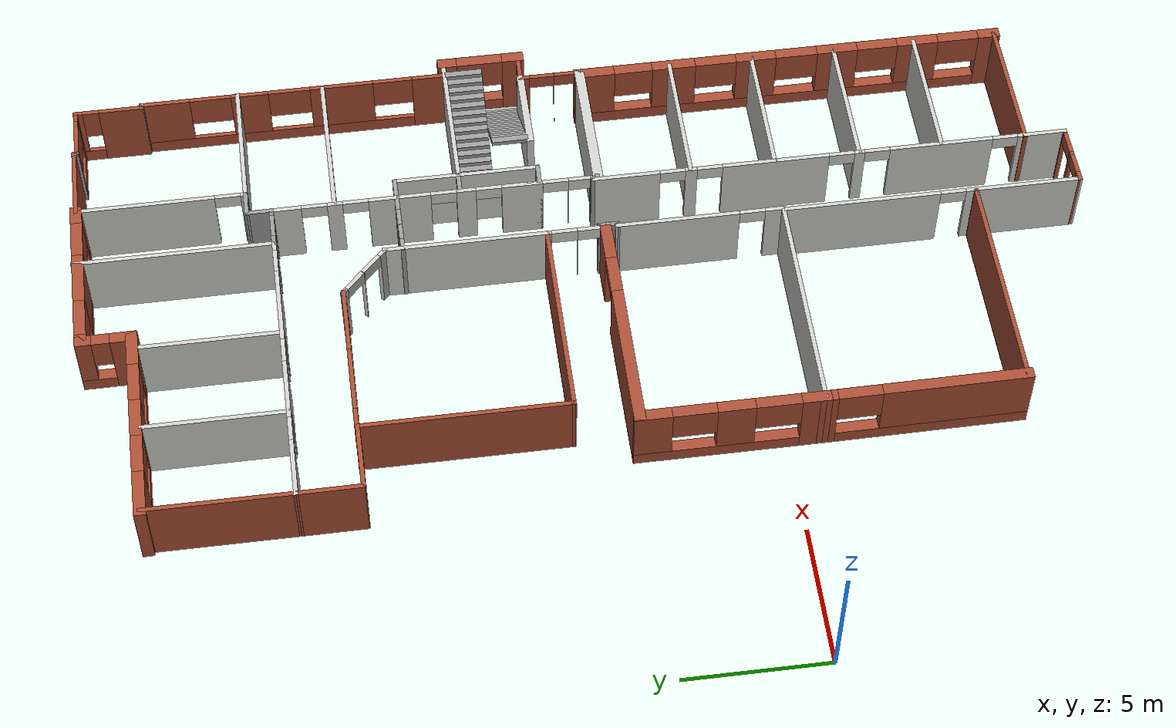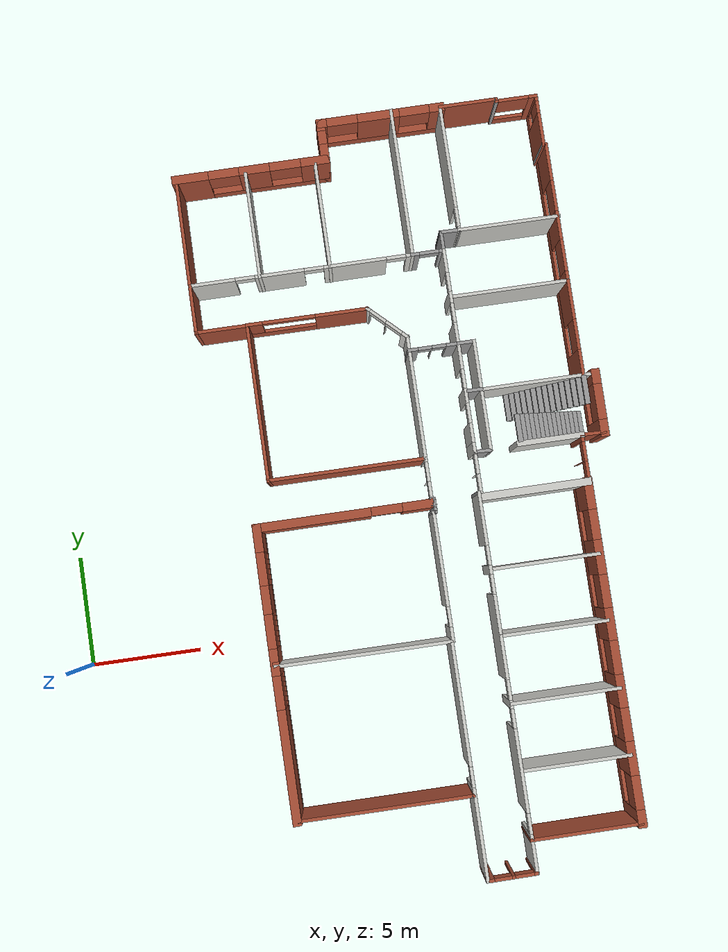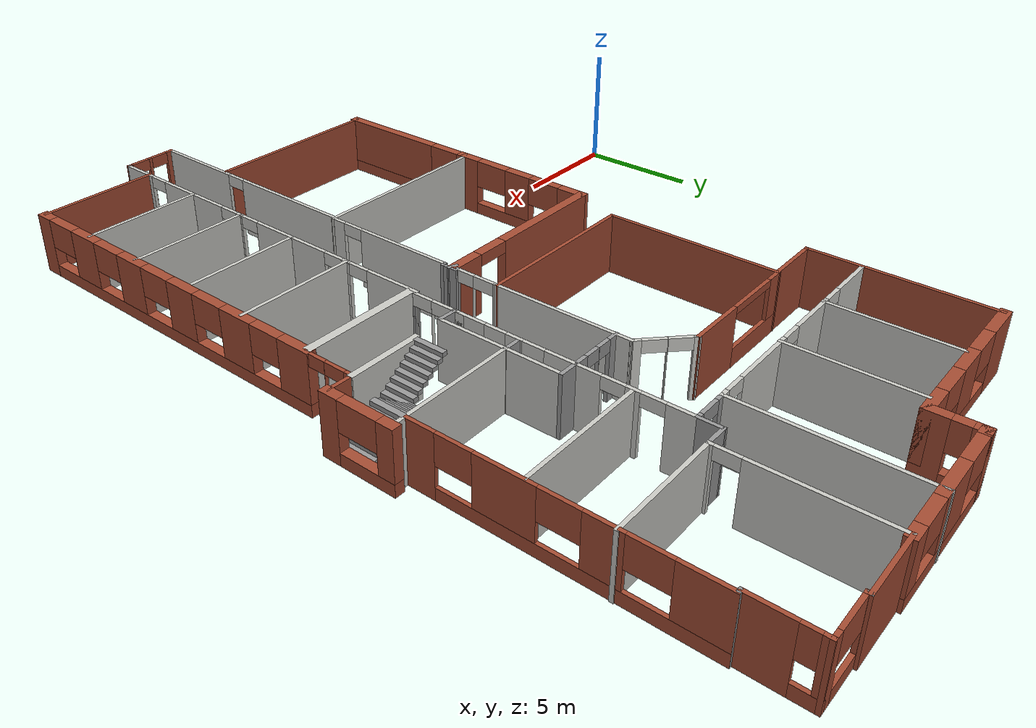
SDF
<?xml version='1.0'?>
<sdf version='1.6'>
  <model name='CVSSP'>
    <pose frame=''>15.8584 5.8407 0 0 -0 0</pose>
    <link name='Stairs_0'>
      <visual name='Stairs_0_Visual_0'>
        <pose frame=''>5.00304 3.34162 0.083333 0 -0 1.5708</pose>
        <geometry>
          <box>
            <size>1.32315 0.233333 0.166667</size>
          </box>
        </geometry>
        <material>
          <script>
            <uri>file://media/materials/scripts/gazebo.material</uri>
            <name>Gazebo/Grey</name>
          </script>
          <ambient>1 1 1 1</ambient>
        </material>
      </visual>
      <collision name='Stairs_0_Collision_0'>
        <geometry>
          <box>
            <size>1.32315 0.233333 0.166667</size>
          </box>
        </geometry>
        <pose frame=''>5.00304 3.34162 0.083333 0 -0 1.5708</pose>
      </collision>
      <visual name='Stairs_0_Visual_1'>
        <pose frame=''>5.23638 3.34162 0.25 0 -0 1.5708</pose>
        <geometry>
          <box>
            <size>1.32315 0.233333 0.166667</size>
          </box>
        </geometry>
        <material>
          <script>
            <uri>file://media/materials/scripts/gazebo.material</uri>
            <name>Gazebo/Grey</name>
          </script>
          <ambient>1 1 1 1</ambient>
        </material>
      </visual>
      <collision name='Stairs_0_Collision_1'>
        <geometry>
          <box>
            <size>1.32315 0.233333 0.166667</size>
          </box>
        </geometry>
        <pose frame=''>5.23638 3.34162 0.25 0 -0 1.5708</pose>
      </collision>
      <visual name='Stairs_0_Visual_2'>
        <pose frame=''>5.46971 3.34162 0.416667 0 -0 1.5708</pose>
        <geometry>
          <box>
            <size>1.32315 0.233333 0.166667</size>
          </box>
        </geometry>
        <material>
          <script>
            <uri>file://media/materials/scripts/gazebo.material</uri>
            <name>Gazebo/Grey</name>
          </script>
          <ambient>1 1 1 1</ambient>
        </material>
      </visual>
      <collision name='Stairs_0_Collision_2'>
        <geometry>
          <box>
            <size>1.32315 0.233333 0.166667</size>
          </box>
        </geometry>
        <pose frame=''>5.46971 3.34162 0.416667 0 -0 1.5708</pose>
      </collision>
      <visual name='Stairs_0_Visual_3'>
        <pose frame=''>5.70304 3.34162 0.583333 0 -0 1.5708</pose>
        <geometry>
          <box>
            <size>1.32315 0.233333 0.166667</size>
          </box>
        </geometry>
        <material>
          <script>
            <uri>file://media/materials/scripts/gazebo.material</uri>
            <name>Gazebo/Grey</name>
          </script>
          <ambient>1 1 1 1</ambient>
        </material>
      </visual>
      <collision name='Stairs_0_Collision_3'>
        <geometry>
          <box>
            <size>1.32315 0.233333 0.166667</size>
          </box>
        </geometry>
        <pose frame=''>5.70304 3.34162 0.583333 0 -0 1.5708</pose>
      </collision>
      <visual name='Stairs_0_Visual_4'>
        <pose frame=''>5.93638 3.34162 0.75 0 -0 1.5708</pose>
        <geometry>
          <box>
            <size>1.32315 0.233333 0.166667</size>
          </box>
        </geometry>
        <material>
          <script>
            <uri>file://media/materials/scripts/gazebo.material</uri>
            <name>Gazebo/Grey</name>
          </script>
          <ambient>1 1 1 1</ambient>
        </material>
      </visual>
      <collision name='Stairs_0_Collision_4'>
        <geometry>
          <box>
            <size>1.32315 0.233333 0.166667</size>
          </box>
        </geometry>
        <pose frame=''>5.93638 3.34162 0.75 0 -0 1.5708</pose>
      </collision>
      <visual name='Stairs_0_Visual_5'>
        <pose frame=''>6.16971 3.34162 0.916667 0 -0 1.5708</pose>
        <geometry>
          <box>
            <size>1.32315 0.233333 0.166667</size>
          </box>
        </geometry>
        <material>
          <script>
            <uri>file://media/materials/scripts/gazebo.material</uri>
            <name>Gazebo/Grey</name>
          </script>
          <ambient>1 1 1 1</ambient>
        </material>
      </visual>
      <collision name='Stairs_0_Collision_5'>
        <geometry>
          <box>
            <size>1.32315 0.233333 0.166667</size>
          </box>
        </geometry>
        <pose frame=''>6.16971 3.34162 0.916667 0 -0 1.5708</pose>
      </collision>
      <visual name='Stairs_0_Visual_6'>
        <pose frame=''>6.40304 3.34162 1.08333 0 -0 1.5708</pose>
        <geometry>
          <box>
            <size>1.32315 0.233333 0.166667</size>
          </box>
        </geometry>
        <material>
          <script>
            <uri>file://media/materials/scripts/gazebo.material</uri>
            <name>Gazebo/Grey</name>
          </script>
          <ambient>1 1 1 1</ambient>
        </material>
      </visual>
      <collision name='Stairs_0_Collision_6'>
        <geometry>
          <box>
            <size>1.32315 0.233333 0.166667</size>
          </box>
        </geometry>
        <pose frame=''>6.40304 3.34162 1.08333 0 -0 1.5708</pose>
      </collision>
      <visual name='Stairs_0_Visual_7'>
        <pose frame=''>6.63638 3.34162 1.25 0 -0 1.5708</pose>
        <geometry>
          <box>
            <size>1.32315 0.233333 0.166667</size>
          </box>
        </geometry>
        <material>
          <script>
            <uri>file://media/materials/scripts/gazebo.material</uri>
            <name>Gazebo/Grey</name>
          </script>
          <ambient>1 1 1 1</ambient>
        </material>
      </visual>
      <collision name='Stairs_0_Collision_7'>
        <geometry>
          <box>
            <size>1.32315 0.233333 0.166667</size>
          </box>
        </geometry>
        <pose frame=''>6.63638 3.34162 1.25 0 -0 1.5708</pose>
      </collision>
      <visual name='Stairs_0_Visual_8'>
        <pose frame=''>6.86971 3.34162 1.41667 0 -0 1.5708</pose>
        <geometry>
          <box>
            <size>1.32315 0.233333 0.166667</size>
          </box>
        </geometry>
        <material>
          <script>
            <uri>file://media/materials/scripts/gazebo.material</uri>
            <name>Gazebo/Grey</name>
          </script>
          <ambient>1 1 1 1</ambient>
        </material>
      </visual>
      <collision name='Stairs_0_Collision_8'>
        <geometry>
          <box>
            <size>1.32315 0.233333 0.166667</size>
          </box>
        </geometry>
        <pose frame=''>6.86971 3.34162 1.41667 0 -0 1.5708</pose>
      </collision>
      <visual name='Stairs_0_Visual_9'>
        <pose frame=''>7.10304 3.34162 1.58333 0 -0 1.5708</pose>
        <geometry>
          <box>
            <size>1.32315 0.233333 0.166667</size>
          </box>
        </geometry>
        <material>
          <script>
            <uri>file://media/materials/scripts/gazebo.material</uri>
            <name>Gazebo/Grey</name>
          </script>
          <ambient>1 1 1 1</ambient>
        </material>
      </visual>
      <collision name='Stairs_0_Collision_9'>
        <geometry>
          <box>
            <size>1.32315 0.233333 0.166667</size>
          </box>
        </geometry>
        <pose frame=''>7.10304 3.34162 1.58333 0 -0 1.5708</pose>
      </collision>
      <visual name='Stairs_0_Visual_10'>
        <pose frame=''>7.33638 3.34162 1.75 0 -0 1.5708</pose>
        <geometry>
          <box>
            <size>1.32315 0.233333 0.166667</size>
          </box>
        </geometry>
        <material>
          <script>
            <uri>file://media/materials/scripts/gazebo.material</uri>
            <name>Gazebo/Grey</name>
          </script>
          <ambient>1 1 1 1</ambient>
        </material>
      </visual>
      <collision name='Stairs_0_Collision_10'>
        <geometry>
          <box>
            <size>1.32315 0.233333 0.166667</size>
          </box>
        </geometry>
        <pose frame=''>7.33638 3.34162 1.75 0 -0 1.5708</pose>
      </collision>
      <visual name='Stairs_0_Visual_11'>
        <pose frame=''>7.56971 3.34162 1.91667 0 -0 1.5708</pose>
        <geometry>
          <box>
            <size>1.32315 0.233333 0.166667</size>
          </box>
        </geometry>
        <material>
          <script>
            <uri>file://media/materials/scripts/gazebo.material</uri>
            <name>Gazebo/Grey</name>
          </script>
          <ambient>1 1 1 1</ambient>
        </material>
      </visual>
      <collision name='Stairs_0_Collision_11'>
        <geometry>
          <box>
            <size>1.32315 0.233333 0.166667</size>
          </box>
        </geometry>
        <pose frame=''>7.56971 3.34162 1.91667 0 -0 1.5708</pose>
      </collision>
      <visual name='Stairs_0_Visual_12'>
        <pose frame=''>7.80304 3.34162 2.08333 0 -0 1.5708</pose>
        <geometry>
          <box>
            <size>1.32315 0.233333 0.166667</size>
          </box>
        </geometry>
        <material>
          <script>
            <uri>file://media/materials/scripts/gazebo.material</uri>
            <name>Gazebo/Grey</name>
          </script>
          <ambient>1 1 1 1</ambient>
        </material>
      </visual>
      <collision name='Stairs_0_Collision_12'>
        <geometry>
          <box>
            <size>1.32315 0.233333 0.166667</size>
          </box>
        </geometry>
        <pose frame=''>7.80304 3.34162 2.08333 0 -0 1.5708</pose>
      </collision>
      <visual name='Stairs_0_Visual_13'>
        <pose frame=''>8.03638 3.34162 2.25 0 -0 1.5708</pose>
        <geometry>
          <box>
            <size>1.32315 0.233333 0.166667</size>
          </box>
        </geometry>
        <material>
          <script>
            <uri>file://media/materials/scripts/gazebo.material</uri>
            <name>Gazebo/Grey</name>
          </script>
          <ambient>1 1 1 1</ambient>
        </material>
      </visual>
      <collision name='Stairs_0_Collision_13'>
        <geometry>
          <box>
            <size>1.32315 0.233333 0.166667</size>
          </box>
        </geometry>
        <pose frame=''>8.03638 3.34162 2.25 0 -0 1.5708</pose>
      </collision>
      <visual name='Stairs_0_Visual_14'>
        <pose frame=''>8.26971 3.34162 2.41667 0 -0 1.5708</pose>
        <geometry>
          <box>
            <size>1.32315 0.233333 0.166667</size>
          </box>
        </geometry>
        <material>
          <script>
            <uri>file://media/materials/scripts/gazebo.material</uri>
            <name>Gazebo/Grey</name>
          </script>
          <ambient>1 1 1 1</ambient>
        </material>
      </visual>
      <collision name='Stairs_0_Collision_14'>
        <geometry>
          <box>
            <size>1.32315 0.233333 0.166667</size>
          </box>
        </geometry>
        <pose frame=''>8.26971 3.34162 2.41667 0 -0 1.5708</pose>
      </collision>
    </link>
    <link name='Stairs_1'>
      <visual name='Stairs_1_Visual_0'>
        <pose frame=''>8.27065 2.04368 0.083333 0 -0 -1.5708</pose>
        <geometry>
          <box>
            <size>1.279 0.233333 0.166667</size>
          </box>
        </geometry>
        <material>
          <script>
            <uri>file://media/materials/scripts/gazebo.material</uri>
            <name>Gazebo/Grey</name>
          </script>
          <ambient>1 1 1 1</ambient>
        </material>
      </visual>
      <collision name='Stairs_1_Collision_0'>
        <geometry>
          <box>
            <size>1.279 0.233333 0.166667</size>
          </box>
        </geometry>
        <pose frame=''>8.27065 2.04368 0.083333 0 -0 -1.5708</pose>
      </collision>
      <visual name='Stairs_1_Visual_1'>
        <pose frame=''>8.03732 2.04368 0.25 0 -0 -1.5708</pose>
        <geometry>
          <box>
            <size>1.279 0.233333 0.166667</size>
          </box>
        </geometry>
        <material>
          <script>
            <uri>file://media/materials/scripts/gazebo.material</uri>
            <name>Gazebo/Grey</name>
          </script>
          <ambient>1 1 1 1</ambient>
        </material>
      </visual>
      <collision name='Stairs_1_Collision_1'>
        <geometry>
          <box>
            <size>1.279 0.233333 0.166667</size>
          </box>
        </geometry>
        <pose frame=''>8.03732 2.04368 0.25 0 -0 -1.5708</pose>
      </collision>
      <visual name='Stairs_1_Visual_2'>
        <pose frame=''>7.80398 2.04368 0.416667 0 -0 -1.5708</pose>
        <geometry>
          <box>
            <size>1.279 0.233333 0.166667</size>
          </box>
        </geometry>
        <material>
          <script>
            <uri>file://media/materials/scripts/gazebo.material</uri>
            <name>Gazebo/Grey</name>
          </script>
          <ambient>1 1 1 1</ambient>
        </material>
      </visual>
      <collision name='Stairs_1_Collision_2'>
        <geometry>
          <box>
            <size>1.279 0.233333 0.166667</size>
          </box>
        </geometry>
        <pose frame=''>7.80398 2.04368 0.416667 0 -0 -1.5708</pose>
      </collision>
      <visual name='Stairs_1_Visual_3'>
        <pose frame=''>7.57065 2.04368 0.583333 0 -0 -1.5708</pose>
        <geometry>
          <box>
            <size>1.279 0.233333 0.166667</size>
          </box>
        </geometry>
        <material>
          <script>
            <uri>file://media/materials/scripts/gazebo.material</uri>
            <name>Gazebo/Grey</name>
          </script>
          <ambient>1 1 1 1</ambient>
        </material>
      </visual>
      <collision name='Stairs_1_Collision_3'>
        <geometry>
          <box>
            <size>1.279 0.233333 0.166667</size>
          </box>
        </geometry>
        <pose frame=''>7.57065 2.04368 0.583333 0 -0 -1.5708</pose>
      </collision>
      <visual name='Stairs_1_Visual_4'>
        <pose frame=''>7.33732 2.04368 0.75 0 -0 -1.5708</pose>
        <geometry>
          <box>
            <size>1.279 0.233333 0.166667</size>
          </box>
        </geometry>
        <material>
          <script>
            <uri>file://media/materials/scripts/gazebo.material</uri>
            <name>Gazebo/Grey</name>
          </script>
          <ambient>1 1 1 1</ambient>
        </material>
      </visual>
      <collision name='Stairs_1_Collision_4'>
        <geometry>
          <box>
            <size>1.279 0.233333 0.166667</size>
          </box>
        </geometry>
        <pose frame=''>7.33732 2.04368 0.75 0 -0 -1.5708</pose>
      </collision>
      <visual name='Stairs_1_Visual_5'>
        <pose frame=''>7.10398 2.04368 0.916667 0 -0 -1.5708</pose>
        <geometry>
          <box>
            <size>1.279 0.233333 0.166667</size>
          </box>
        </geometry>
        <material>
          <script>
            <uri>file://media/materials/scripts/gazebo.material</uri>
            <name>Gazebo/Grey</name>
          </script>
          <ambient>1 1 1 1</ambient>
        </material>
      </visual>
      <collision name='Stairs_1_Collision_5'>
        <geometry>
          <box>
            <size>1.279 0.233333 0.166667</size>
          </box>
        </geometry>
        <pose frame=''>7.10398 2.04368 0.916667 0 -0 -1.5708</pose>
      </collision>
      <visual name='Stairs_1_Visual_6'>
        <pose frame=''>6.87065 2.04368 1.08333 0 -0 -1.5708</pose>
        <geometry>
          <box>
            <size>1.279 0.233333 0.166667</size>
          </box>
        </geometry>
        <material>
          <script>
            <uri>file://media/materials/scripts/gazebo.material</uri>
            <name>Gazebo/Grey</name>
          </script>
          <ambient>1 1 1 1</ambient>
        </material>
      </visual>
      <collision name='Stairs_1_Collision_6'>
        <geometry>
          <box>
            <size>1.279 0.233333 0.166667</size>
          </box>
        </geometry>
        <pose frame=''>6.87065 2.04368 1.08333 0 -0 -1.5708</pose>
      </collision>
      <visual name='Stairs_1_Visual_7'>
        <pose frame=''>6.63732 2.04368 1.25 0 -0 -1.5708</pose>
        <geometry>
          <box>
            <size>1.279 0.233333 0.166667</size>
          </box>
        </geometry>
        <material>
          <script>
            <uri>file://media/materials/scripts/gazebo.material</uri>
            <name>Gazebo/Grey</name>
          </script>
          <ambient>1 1 1 1</ambient>
        </material>
      </visual>
      <collision name='Stairs_1_Collision_7'>
        <geometry>
          <box>
            <size>1.279 0.233333 0.166667</size>
          </box>
        </geometry>
        <pose frame=''>6.63732 2.04368 1.25 0 -0 -1.5708</pose>
      </collision>
      <visual name='Stairs_1_Visual_8'>
        <pose frame=''>6.40398 2.04368 1.41667 0 -0 -1.5708</pose>
        <geometry>
          <box>
            <size>1.279 0.233333 0.166667</size>
          </box>
        </geometry>
        <material>
          <script>
            <uri>file://media/materials/scripts/gazebo.material</uri>
            <name>Gazebo/Grey</name>
          </script>
          <ambient>1 1 1 1</ambient>
        </material>
      </visual>
      <collision name='Stairs_1_Collision_8'>
        <geometry>
          <box>
            <size>1.279 0.233333 0.166667</size>
          </box>
        </geometry>
        <pose frame=''>6.40398 2.04368 1.41667 0 -0 -1.5708</pose>
      </collision>
      <visual name='Stairs_1_Visual_9'>
        <pose frame=''>6.17065 2.04368 1.58333 0 -0 -1.5708</pose>
        <geometry>
          <box>
            <size>1.279 0.233333 0.166667</size>
          </box>
        </geometry>
        <material>
          <script>
            <uri>file://media/materials/scripts/gazebo.material</uri>
            <name>Gazebo/Grey</name>
          </script>
          <ambient>1 1 1 1</ambient>
        </material>
      </visual>
      <collision name='Stairs_1_Collision_9'>
        <geometry>
          <box>
            <size>1.279 0.233333 0.166667</size>
          </box>
        </geometry>
        <pose frame=''>6.17065 2.04368 1.58333 0 -0 -1.5708</pose>
      </collision>
      <visual name='Stairs_1_Visual_10'>
        <pose frame=''>5.93732 2.04368 1.75 0 -0 -1.5708</pose>
        <geometry>
          <box>
            <size>1.279 0.233333 0.166667</size>
          </box>
        </geometry>
        <material>
          <script>
            <uri>file://media/materials/scripts/gazebo.material</uri>
            <name>Gazebo/Grey</name>
          </script>
          <ambient>1 1 1 1</ambient>
        </material>
      </visual>
      <collision name='Stairs_1_Collision_10'>
        <geometry>
          <box>
            <size>1.279 0.233333 0.166667</size>
          </box>
        </geometry>
        <pose frame=''>5.93732 2.04368 1.75 0 -0 -1.5708</pose>
      </collision>
      <visual name='Stairs_1_Visual_11'>
        <pose frame=''>5.70398 2.04368 1.91667 0 -0 -1.5708</pose>
        <geometry>
          <box>
            <size>1.279 0.233333 0.166667</size>
          </box>
        </geometry>
        <material>
          <script>
            <uri>file://media/materials/scripts/gazebo.material</uri>
            <name>Gazebo/Grey</name>
          </script>
          <ambient>1 1 1 1</ambient>
        </material>
      </visual>
      <collision name='Stairs_1_Collision_11'>
        <geometry>
          <box>
            <size>1.279 0.233333 0.166667</size>
          </box>
        </geometry>
        <pose frame=''>5.70398 2.04368 1.91667 0 -0 -1.5708</pose>
      </collision>
      <visual name='Stairs_1_Visual_12'>
        <pose frame=''>5.47065 2.04368 2.08333 0 -0 -1.5708</pose>
        <geometry>
          <box>
            <size>1.279 0.233333 0.166667</size>
          </box>
        </geometry>
        <material>
          <script>
            <uri>file://media/materials/scripts/gazebo.material</uri>
            <name>Gazebo/Grey</name>
          </script>
          <ambient>1 1 1 1</ambient>
        </material>
      </visual>
      <collision name='Stairs_1_Collision_12'>
        <geometry>
          <box>
            <size>1.279 0.233333 0.166667</size>
          </box>
        </geometry>
        <pose frame=''>5.47065 2.04368 2.08333 0 -0 -1.5708</pose>
      </collision>
      <visual name='Stairs_1_Visual_13'>
        <pose frame=''>5.23732 2.04368 2.25 0 -0 -1.5708</pose>
        <geometry>
          <box>
            <size>1.279 0.233333 0.166667</size>
          </box>
        </geometry>
        <material>
          <script>
            <uri>file://media/materials/scripts/gazebo.material</uri>
            <name>Gazebo/Grey</name>
          </script>
          <ambient>1 1 1 1</ambient>
        </material>
      </visual>
      <collision name='Stairs_1_Collision_13'>
        <geometry>
          <box>
            <size>1.279 0.233333 0.166667</size>
          </box>
        </geometry>
        <pose frame=''>5.23732 2.04368 2.25 0 -0 -1.5708</pose>
      </collision>
      <visual name='Stairs_1_Visual_14'>
        <pose frame=''>5.00398 2.04368 2.41667 0 -0 -1.5708</pose>
        <geometry>
          <box>
            <size>1.279 0.233333 0.166667</size>
          </box>
        </geometry>
        <material>
          <script>
            <uri>file://media/materials/scripts/gazebo.material</uri>
            <name>Gazebo/Grey</name>
          </script>
          <ambient>1 1 1 1</ambient>
        </material>
      </visual>
      <collision name='Stairs_1_Collision_14'>
        <geometry>
          <box>
            <size>1.279 0.233333 0.166667</size>
          </box>
        </geometry>
        <pose frame=''>5.00398 2.04368 2.41667 0 -0 -1.5708</pose>
      </collision>
    </link>
    <link name='Wall_0'>
      <collision name='Wall_0_Collision'>
        <geometry>
          <box>
            <size>7.30534 0.15 2.5</size>
          </box>
        </geometry>
        <pose frame=''>0 0 1.25 0 -0 0</pose>
      </collision>
      <visual name='Wall_0_Visual'>
        <pose frame=''>0 0 1.25 0 -0 0</pose>
        <geometry>
          <box>
            <size>7.30534 0.15 2.5</size>
          </box>
        </geometry>
        <material>
          <script>
            <uri>file://media/materials/scripts/gazebo.material</uri>
            <name>Gazebo/Bricks</name>
          </script>
          <ambient>1 1 1 1</ambient>
        </material>
      </visual>
      <pose frame=''>-6.50608 4.87105 0 0 0 -1.57292</pose>
    </link>
    <link name='Wall_1'>
      <collision name='Wall_1_Collision'>
        <geometry>
          <box>
            <size>7.29881 0.15 2.5</size>
          </box>
        </geometry>
        <pose frame=''>0 0 1.25 0 -0 0</pose>
      </collision>
      <visual name='Wall_1_Visual'>
        <pose frame=''>0 0 1.25 0 -0 0</pose>
        <geometry>
          <box>
            <size>7.29881 0.15 2.5</size>
          </box>
        </geometry>
        <material>
          <script>
            <uri>file://media/materials/scripts/gazebo.material</uri>
            <name>Gazebo/Bricks</name>
          </script>
          <ambient>1 1 1 1</ambient>
        </material>
      </visual>
      <pose frame=''>-2.93929 1.28682 0 0 0 -0.001839</pose>
    </link>
    <link name='Wall_124'>
      <pose frame=''>8.26569 9.43515 0 0 -0 1.5708</pose>
      <visual name='Wall_124_Visual_0'>
        <pose frame=''>-4.86749 0 1.25 0 -0 0</pose>
        <geometry>
          <box>
            <size>1.26502 0.15 2.5</size>
          </box>
        </geometry>
        <material>
          <script>
            <uri>file://media/materials/scripts/gazebo.material</uri>
            <name>Gazebo/Bricks</name>
          </script>
          <ambient>1 1 1 1</ambient>
        </material>
      </visual>
      <collision name='Wall_124_Collision_0'>
        <geometry>
          <box>
            <size>1.26502 0.15 2.5</size>
          </box>
        </geometry>
        <pose frame=''>-4.86749 0 1.25 0 -0 0</pose>
      </collision>
      <visual name='Wall_124_Visual_1'>
        <pose frame=''>0.632508 0 0.25 0 -0 0</pose>
        <geometry>
          <box>
            <size>9.73498 0.15 0.5</size>
          </box>
        </geometry>
        <material>
          <script>
            <uri>file://media/materials/scripts/gazebo.material</uri>
            <name>Gazebo/Bricks</name>
          </script>
          <ambient>1 1 1 1</ambient>
        </material>
      </visual>
      <collision name='Wall_124_Collision_1'>
        <geometry>
          <box>
            <size>9.73498 0.15 0.5</size>
          </box>
        </geometry>
        <pose frame=''>0.632508 0 0.25 0 -0 0</pose>
      </collision>
      <visual name='Wall_124_Visual_2'>
        <pose frame=''>-1.69625 0 1.5 0 -0 0</pose>
        <geometry>
          <box>
            <size>2.26535 0.15 2</size>
          </box>
        </geometry>
        <material>
          <script>
            <uri>file://media/materials/scripts/gazebo.material</uri>
            <name>Gazebo/Bricks</name>
          </script>
          <ambient>1 1 1 1</ambient>
        </material>
      </visual>
      <collision name='Wall_124_Collision_2'>
        <geometry>
          <box>
            <size>2.26535 0.15 2</size>
          </box>
        </geometry>
        <pose frame=''>-1.69625 0 1.5 0 -0 0</pose>
      </collision>
      <visual name='Wall_124_Visual_3'>
        <pose frame=''>1.59133 0 1.5 0 -0 0</pose>
        <geometry>
          <box>
            <size>1.3376 0.15 2</size>
          </box>
        </geometry>
        <material>
          <script>
            <uri>file://media/materials/scripts/gazebo.material</uri>
            <name>Gazebo/Bricks</name>
          </script>
          <ambient>1 1 1 1</ambient>
        </material>
      </visual>
      <collision name='Wall_124_Collision_3'>
        <geometry>
          <box>
            <size>1.3376 0.15 2</size>
          </box>
        </geometry>
        <pose frame=''>1.59133 0 1.5 0 -0 0</pose>
      </collision>
      <visual name='Wall_124_Visual_4'>
        <pose frame=''>4.61168 0 1.5 0 -0 0</pose>
        <geometry>
          <box>
            <size>1.77663 0.15 2</size>
          </box>
        </geometry>
        <material>
          <script>
            <uri>file://media/materials/scripts/gazebo.material</uri>
            <name>Gazebo/Bricks</name>
          </script>
          <ambient>1 1 1 1</ambient>
        </material>
      </visual>
      <collision name='Wall_124_Collision_4'>
        <geometry>
          <box>
            <size>1.77663 0.15 2</size>
          </box>
        </geometry>
        <pose frame=''>4.61168 0 1.5 0 -0 0</pose>
      </collision>
      <visual name='Wall_124_Visual_5'>
        <pose frame=''>-3.53196 0 1.9 0 -0 0</pose>
        <geometry>
          <box>
            <size>1.40606 0.15 1.2</size>
          </box>
        </geometry>
        <material>
          <script>
            <uri>file://media/materials/scripts/gazebo.material</uri>
            <name>Gazebo/Bricks</name>
          </script>
          <ambient>1 1 1 1</ambient>
        </material>
      </visual>
      <collision name='Wall_124_Collision_5'>
        <geometry>
          <box>
            <size>1.40606 0.15 1.2</size>
          </box>
        </geometry>
        <pose frame=''>-3.53196 0 1.9 0 -0 0</pose>
      </collision>
      <visual name='Wall_124_Visual_6'>
        <pose frame=''>0.179474 0 1.9 0 -0 0</pose>
        <geometry>
          <box>
            <size>1.4861 0.15 1.2</size>
          </box>
        </geometry>
        <material>
          <script>
            <uri>file://media/materials/scripts/gazebo.material</uri>
            <name>Gazebo/Bricks</name>
          </script>
          <ambient>1 1 1 1</ambient>
        </material>
      </visual>
      <collision name='Wall_124_Collision_6'>
        <geometry>
          <box>
            <size>1.4861 0.15 1.2</size>
          </box>
        </geometry>
        <pose frame=''>0.179474 0 1.9 0 -0 0</pose>
      </collision>
      <visual name='Wall_124_Visual_7'>
        <pose frame=''>2.99175 0 1.9 0 -0 0</pose>
        <geometry>
          <box>
            <size>1.46323 0.15 1.2</size>
          </box>
        </geometry>
        <material>
          <script>
            <uri>file://media/materials/scripts/gazebo.material</uri>
            <name>Gazebo/Bricks</name>
          </script>
          <ambient>1 1 1 1</ambient>
        </material>
      </visual>
      <collision name='Wall_124_Collision_7'>
        <geometry>
          <box>
            <size>1.46323 0.15 1.2</size>
          </box>
        </geometry>
        <pose frame=''>2.99175 0 1.9 0 -0 0</pose>
      </collision>
    </link>
    <link name='Wall_125'>
      <collision name='Wall_125_Collision'>
        <geometry>
          <box>
            <size>0.240056 0.15 2.5</size>
          </box>
        </geometry>
        <pose frame=''>0 0 1.25 0 -0 0</pose>
      </collision>
      <visual name='Wall_125_Visual'>
        <pose frame=''>0 0 1.25 0 -0 0</pose>
        <geometry>
          <box>
            <size>0.240056 0.15 2.5</size>
          </box>
        </geometry>
        <material>
          <script>
            <uri>file://media/materials/scripts/gazebo.material</uri>
            <name>Gazebo/Grey</name>
          </script>
          <ambient>1 1 1 1</ambient>
        </material>
      </visual>
      <pose frame=''>8.21072 14.8602 0 0 -0 3.14159</pose>
    </link>
    <link name='Wall_126'>
      <pose frame=''>8.16569 16.0351 0 0 -0 1.5708</pose>
      <visual name='Wall_126_Visual_0'>
        <pose frame=''>-0.445028 0 1.25 0 -0 0</pose>
        <geometry>
          <box>
            <size>1.60994 0.15 2.5</size>
          </box>
        </geometry>
        <material>
          <script>
            <uri>file://media/materials/scripts/gazebo.material</uri>
            <name>Gazebo/Bricks</name>
          </script>
          <ambient>1 1 1 1</ambient>
        </material>
      </visual>
      <collision name='Wall_126_Collision_0'>
        <geometry>
          <box>
            <size>1.60994 0.15 2.5</size>
          </box>
        </geometry>
        <pose frame=''>-0.445028 0 1.25 0 -0 0</pose>
      </collision>
      <visual name='Wall_126_Visual_1'>
        <pose frame=''>0.804972 0 0.25 0 -0 0</pose>
        <geometry>
          <box>
            <size>0.890056 0.15 0.5</size>
          </box>
        </geometry>
        <material>
          <script>
            <uri>file://media/materials/scripts/gazebo.material</uri>
            <name>Gazebo/Bricks</name>
          </script>
          <ambient>1 1 1 1</ambient>
        </material>
      </visual>
      <collision name='Wall_126_Collision_1'>
        <geometry>
          <box>
            <size>0.890056 0.15 0.5</size>
          </box>
        </geometry>
        <pose frame=''>0.804972 0 0.25 0 -0 0</pose>
      </collision>
      <visual name='Wall_126_Visual_2'>
        <pose frame=''>1.09062 0 1.5 0 -0 0</pose>
        <geometry>
          <box>
            <size>0.318757 0.15 2</size>
          </box>
        </geometry>
        <material>
          <script>
            <uri>file://media/materials/scripts/gazebo.material</uri>
            <name>Gazebo/Bricks</name>
          </script>
          <ambient>1 1 1 1</ambient>
        </material>
      </visual>
      <collision name='Wall_126_Collision_2'>
        <geometry>
          <box>
            <size>0.318757 0.15 2</size>
          </box>
        </geometry>
        <pose frame=''>1.09062 0 1.5 0 -0 0</pose>
      </collision>
      <visual name='Wall_126_Visual_3'>
        <pose frame=''>0.645594 0 1.9 0 -0 0</pose>
        <geometry>
          <box>
            <size>0.571299 0.15 1.2</size>
          </box>
        </geometry>
        <material>
          <script>
            <uri>file://media/materials/scripts/gazebo.material</uri>
            <name>Gazebo/Bricks</name>
          </script>
          <ambient>1 1 1 1</ambient>
        </material>
      </visual>
      <collision name='Wall_126_Collision_3'>
        <geometry>
          <box>
            <size>0.571299 0.15 1.2</size>
          </box>
        </geometry>
        <pose frame=''>0.645594 0 1.9 0 -0 0</pose>
      </collision>
    </link>
    <link name='Wall_127'>
      <pose frame=''>7.24069 17.2101 0 0 -0 3.14159</pose>
      <visual name='Wall_127_Visual_0'>
        <pose frame=''>-0.790859 0 1.25 0 -0 0</pose>
        <geometry>
          <box>
            <size>0.418283 0.15 2.5</size>
          </box>
        </geometry>
        <material>
          <script>
            <uri>file://media/materials/scripts/gazebo.material</uri>
            <name>Gazebo/Bricks</name>
          </script>
          <ambient>1 1 1 1</ambient>
        </material>
      </visual>
      <collision name='Wall_127_Collision_0'>
        <geometry>
          <box>
            <size>0.418283 0.15 2.5</size>
          </box>
        </geometry>
        <pose frame=''>-0.790859 0 1.25 0 -0 0</pose>
      </collision>
      <visual name='Wall_127_Visual_1'>
        <pose frame=''>0.209141 0 0.25 0 -0 0</pose>
        <geometry>
          <box>
            <size>1.58172 0.15 0.5</size>
          </box>
        </geometry>
        <material>
          <script>
            <uri>file://media/materials/scripts/gazebo.material</uri>
            <name>Gazebo/Bricks</name>
          </script>
          <ambient>1 1 1 1</ambient>
        </material>
      </visual>
      <collision name='Wall_127_Collision_1'>
        <geometry>
          <box>
            <size>1.58172 0.15 0.5</size>
          </box>
        </geometry>
        <pose frame=''>0.209141 0 0.25 0 -0 0</pose>
      </collision>
      <visual name='Wall_127_Visual_2'>
        <pose frame=''>0.917888 0 1.5 0 -0 0</pose>
        <geometry>
          <box>
            <size>0.164224 0.15 2</size>
          </box>
        </geometry>
        <material>
          <script>
            <uri>file://media/materials/scripts/gazebo.material</uri>
            <name>Gazebo/Bricks</name>
          </script>
          <ambient>1 1 1 1</ambient>
        </material>
      </visual>
      <collision name='Wall_127_Collision_2'>
        <geometry>
          <box>
            <size>0.164224 0.15 2</size>
          </box>
        </geometry>
        <pose frame=''>0.917888 0 1.5 0 -0 0</pose>
      </collision>
      <visual name='Wall_127_Visual_3'>
        <pose frame=''>0.127029 0 1.9 0 -0 0</pose>
        <geometry>
          <box>
            <size>1.41749 0.15 1.2</size>
          </box>
        </geometry>
        <material>
          <script>
            <uri>file://media/materials/scripts/gazebo.material</uri>
            <name>Gazebo/Bricks</name>
          </script>
          <ambient>1 1 1 1</ambient>
        </material>
      </visual>
      <collision name='Wall_127_Collision_3'>
        <geometry>
          <box>
            <size>1.41749 0.15 1.2</size>
          </box>
        </geometry>
        <pose frame=''>0.127029 0 1.9 0 -0 0</pose>
      </collision>
    </link>
    <link name='Wall_128'>
      <collision name='Wall_128_Collision'>
        <geometry>
          <box>
            <size>0.25 0.15 2.5</size>
          </box>
        </geometry>
        <pose frame=''>0 0 1.25 0 -0 0</pose>
      </collision>
      <visual name='Wall_128_Visual'>
        <pose frame=''>0 0 1.25 0 -0 0</pose>
        <geometry>
          <box>
            <size>0.25 0.15 2.5</size>
          </box>
        </geometry>
        <material>
          <script>
            <uri>file://media/materials/scripts/gazebo.material</uri>
            <name>Gazebo/Grey</name>
          </script>
          <ambient>1 1 1 1</ambient>
        </material>
      </visual>
      <pose frame=''>6.31569 17.2601 0 0 -0 1.5708</pose>
    </link>
    <link name='Wall_129'>
      <collision name='Wall_129_Collision'>
        <geometry>
          <box>
            <size>2.76709 0.15 2.5</size>
          </box>
        </geometry>
        <pose frame=''>0 0 1.25 0 -0 0</pose>
      </collision>
      <visual name='Wall_129_Visual'>
        <pose frame=''>0 0 1.25 0 -0 0</pose>
        <geometry>
          <box>
            <size>2.76709 0.15 2.5</size>
          </box>
        </geometry>
        <material>
          <script>
            <uri>file://media/materials/scripts/gazebo.material</uri>
            <name>Gazebo/Bricks</name>
          </script>
          <ambient>1 1 1 1</ambient>
        </material>
      </visual>
      <pose frame=''>5.00715 17.3102 0 0 -0 3.14153</pose>
    </link>
    <link name='Wall_13'>
      <pose frame=''>1.74828 6.25397 0 0 -0 0.002327</pose>
      <visual name='Wall_13_Visual_0'>
        <pose frame=''>-0.957237 0 1.25 0 -0 0</pose>
        <geometry>
          <box>
            <size>0.497877 0.15 2.5</size>
          </box>
        </geometry>
        <material>
          <script>
            <uri>file://media/materials/scripts/gazebo.material</uri>
            <name>Gazebo/Grey</name>
          </script>
          <ambient>1 1 1 1</ambient>
        </material>
      </visual>
      <collision name='Wall_13_Collision_0'>
        <geometry>
          <box>
            <size>0.497877 0.15 2.5</size>
          </box>
        </geometry>
        <pose frame=''>-0.957237 0 1.25 0 -0 0</pose>
      </collision>
      <visual name='Wall_13_Visual_1'>
        <pose frame=''>-0.078249 0 1.25 0 -0 0</pose>
        <geometry>
          <box>
            <size>0.008926 0.15 2.5</size>
          </box>
        </geometry>
        <material>
          <script>
            <uri>file://media/materials/scripts/gazebo.material</uri>
            <name>Gazebo/Grey</name>
          </script>
          <ambient>1 1 1 1</ambient>
        </material>
      </visual>
      <collision name='Wall_13_Collision_1'>
        <geometry>
          <box>
            <size>0.008926 0.15 2.5</size>
          </box>
        </geometry>
        <pose frame=''>-0.078249 0 1.25 0 -0 0</pose>
      </collision>
      <visual name='Wall_13_Visual_2'>
        <pose frame=''>0.890476 0 1.25 0 -0 0</pose>
        <geometry>
          <box>
            <size>0.631399 0.15 2.5</size>
          </box>
        </geometry>
        <material>
          <script>
            <uri>file://media/materials/scripts/gazebo.material</uri>
            <name>Gazebo/Grey</name>
          </script>
          <ambient>1 1 1 1</ambient>
        </material>
      </visual>
      <collision name='Wall_13_Collision_2'>
        <geometry>
          <box>
            <size>0.631399 0.15 2.5</size>
          </box>
        </geometry>
        <pose frame=''>0.890476 0 1.25 0 -0 0</pose>
      </collision>
      <visual name='Wall_13_Visual_3'>
        <pose frame=''>-0.395505 0 2.25 0 -0 0</pose>
        <geometry>
          <box>
            <size>0.625586 0.15 0.5</size>
          </box>
        </geometry>
        <material>
          <script>
            <uri>file://media/materials/scripts/gazebo.material</uri>
            <name>Gazebo/Grey</name>
          </script>
          <ambient>1 1 1 1</ambient>
        </material>
      </visual>
      <collision name='Wall_13_Collision_3'>
        <geometry>
          <box>
            <size>0.625586 0.15 0.5</size>
          </box>
        </geometry>
        <pose frame=''>-0.395505 0 2.25 0 -0 0</pose>
      </collision>
      <visual name='Wall_13_Visual_4'>
        <pose frame=''>0.250495 0 2.25 0 -0 0</pose>
        <geometry>
          <box>
            <size>0.648562 0.15 0.5</size>
          </box>
        </geometry>
        <material>
          <script>
            <uri>file://media/materials/scripts/gazebo.material</uri>
            <name>Gazebo/Grey</name>
          </script>
          <ambient>1 1 1 1</ambient>
        </material>
      </visual>
      <collision name='Wall_13_Collision_4'>
        <geometry>
          <box>
            <size>0.648562 0.15 0.5</size>
          </box>
        </geometry>
        <pose frame=''>0.250495 0 2.25 0 -0 0</pose>
      </collision>
    </link>
    <link name='Wall_130'>
      <pose frame=''>3.70715 14.3803 0 0 0 -1.56788</pose>
      <visual name='Wall_130_Visual_0'>
        <pose frame=''>-0.573725 0 1.25 0 -0 0</pose>
        <geometry>
          <box>
            <size>4.86265 0.15 2.5</size>
          </box>
        </geometry>
        <material>
          <script>
            <uri>file://media/materials/scripts/gazebo.material</uri>
            <name>Gazebo/CeilingTiled</name>
          </script>
          <ambient>1 1 1 1</ambient>
        </material>
      </visual>
      <collision name='Wall_130_Collision_0'>
        <geometry>
          <box>
            <size>4.86265 0.15 2.5</size>
          </box>
        </geometry>
        <pose frame=''>-0.573725 0 1.25 0 -0 0</pose>
      </collision>
      <visual name='Wall_130_Visual_1'>
        <pose frame=''>2.88132 0 1.25 0 -0 0</pose>
        <geometry>
          <box>
            <size>0.24745 0.15 2.5</size>
          </box>
        </geometry>
        <material>
          <script>
            <uri>file://media/materials/scripts/gazebo.material</uri>
            <name>Gazebo/CeilingTiled</name>
          </script>
          <ambient>1 1 1 1</ambient>
        </material>
      </visual>
      <collision name='Wall_130_Collision_1'>
        <geometry>
          <box>
            <size>0.24745 0.15 2.5</size>
          </box>
        </geometry>
        <pose frame=''>2.88132 0 1.25 0 -0 0</pose>
      </collision>
      <visual name='Wall_130_Visual_2'>
        <pose frame=''>2.3076 0 2.25 0 -0 0</pose>
        <geometry>
          <box>
            <size>0.9 0.15 0.5</size>
          </box>
        </geometry>
        <material>
          <script>
            <uri>file://media/materials/scripts/gazebo.material</uri>
            <name>Gazebo/CeilingTiled</name>
          </script>
          <ambient>1 1 1 1</ambient>
        </material>
      </visual>
      <collision name='Wall_130_Collision_2'>
        <geometry>
          <box>
            <size>0.9 0.15 0.5</size>
          </box>
        </geometry>
        <pose frame=''>2.3076 0 2.25 0 -0 0</pose>
      </collision>
    </link>
    <link name='Wall_131'>
      <collision name='Wall_131_Collision'>
        <geometry>
          <box>
            <size>1.00006 0.15 2.5</size>
          </box>
        </geometry>
        <pose frame=''>0 0 1.25 0 -0 0</pose>
      </collision>
      <visual name='Wall_131_Visual'>
        <pose frame=''>0 0 1.25 0 -0 0</pose>
        <geometry>
          <box>
            <size>1.00006 0.15 2.5</size>
          </box>
        </geometry>
        <material>
          <script>
            <uri>file://media/materials/scripts/gazebo.material</uri>
            <name>Gazebo/Grey</name>
          </script>
          <ambient>1 1 1 1</ambient>
        </material>
      </visual>
      <pose frame=''>3.29069 11.4552 0 0 -0 3.12989</pose>
    </link>
    <link name='Wall_132'>
      <collision name='Wall_132_Collision'>
        <geometry>
          <box>
            <size>1 0.15 2.5</size>
          </box>
        </geometry>
        <pose frame=''>0 0 1.25 0 -0 0</pose>
      </collision>
      <visual name='Wall_132_Visual'>
        <pose frame=''>0 0 1.25 0 -0 0</pose>
        <geometry>
          <box>
            <size>1 0.15 2.5</size>
          </box>
        </geometry>
        <material>
          <script>
            <uri>file://media/materials/scripts/gazebo.material</uri>
            <name>Gazebo/Grey</name>
          </script>
          <ambient>1 1 1 1</ambient>
        </material>
      </visual>
      <pose frame=''>2.86569 11.0351 0 0 0 -1.5708</pose>
    </link>
    <link name='Wall_133'>
      <pose frame=''>2.13851 10.6102 0 0 -0 3.14159</pose>
      <visual name='Wall_133_Visual_0'>
        <pose frame=''>-0.654159 0 1.25 0 -0 0</pose>
        <geometry>
          <box>
            <size>0.296029 0.15 2.5</size>
          </box>
        </geometry>
        <material>
          <script>
            <uri>file://media/materials/scripts/gazebo.material</uri>
            <name>Gazebo/Grey</name>
          </script>
          <ambient>1 1 1 1</ambient>
        </material>
      </visual>
      <collision name='Wall_133_Collision_0'>
        <geometry>
          <box>
            <size>0.296029 0.15 2.5</size>
          </box>
        </geometry>
        <pose frame=''>-0.654159 0 1.25 0 -0 0</pose>
      </collision>
      <visual name='Wall_133_Visual_1'>
        <pose frame=''>0.598015 0 1.25 0 -0 0</pose>
        <geometry>
          <box>
            <size>0.408319 0.15 2.5</size>
          </box>
        </geometry>
        <material>
          <script>
            <uri>file://media/materials/scripts/gazebo.material</uri>
            <name>Gazebo/Grey</name>
          </script>
          <ambient>1 1 1 1</ambient>
        </material>
      </visual>
      <collision name='Wall_133_Collision_1'>
        <geometry>
          <box>
            <size>0.408319 0.15 2.5</size>
          </box>
        </geometry>
        <pose frame=''>0.598015 0 1.25 0 -0 0</pose>
      </collision>
      <visual name='Wall_133_Visual_2'>
        <pose frame=''>-0.056145 0 2.25 0 -0 0</pose>
        <geometry>
          <box>
            <size>0.9 0.15 0.5</size>
          </box>
        </geometry>
        <material>
          <script>
            <uri>file://media/materials/scripts/gazebo.material</uri>
            <name>Gazebo/Grey</name>
          </script>
          <ambient>1 1 1 1</ambient>
        </material>
      </visual>
      <collision name='Wall_133_Collision_2'>
        <geometry>
          <box>
            <size>0.9 0.15 0.5</size>
          </box>
        </geometry>
        <pose frame=''>-0.056145 0 2.25 0 -0 0</pose>
      </collision>
    </link>
    <link name='Wall_134'>
      <pose frame=''>-3.71148 10.6102 0 0 -0 3.14159</pose>
      <visual name='Wall_134_Visual_0'>
        <pose frame=''>-5.01383 0 1.25 0 -0 0</pose>
        <geometry>
          <box>
            <size>0.367986 0.15 2.5</size>
          </box>
        </geometry>
        <material>
          <script>
            <uri>file://media/materials/scripts/gazebo.material</uri>
            <name>Gazebo/CeilingTiled</name>
          </script>
          <ambient>1 1 1 1</ambient>
        </material>
      </visual>
      <collision name='Wall_134_Collision_0'>
        <geometry>
          <box>
            <size>0.367986 0.15 2.5</size>
          </box>
        </geometry>
        <pose frame=''>-5.01383 0 1.25 0 -0 0</pose>
      </collision>
      <visual name='Wall_134_Visual_1'>
        <pose frame=''>-2.48136 0 1.25 0 -0 0</pose>
        <geometry>
          <box>
            <size>2.89696 0.15 2.5</size>
          </box>
        </geometry>
        <material>
          <script>
            <uri>file://media/materials/scripts/gazebo.material</uri>
            <name>Gazebo/CeilingTiled</name>
          </script>
          <ambient>1 1 1 1</ambient>
        </material>
      </visual>
      <collision name='Wall_134_Collision_1'>
        <geometry>
          <box>
            <size>2.89696 0.15 2.5</size>
          </box>
        </geometry>
        <pose frame=''>-2.48136 0 1.25 0 -0 0</pose>
      </collision>
      <visual name='Wall_134_Visual_2'>
        <pose frame=''>1.00237 0 1.25 0 -0 0</pose>
        <geometry>
          <box>
            <size>2.27049 0.15 2.5</size>
          </box>
        </geometry>
        <material>
          <script>
            <uri>file://media/materials/scripts/gazebo.material</uri>
            <name>Gazebo/CeilingTiled</name>
          </script>
          <ambient>1 1 1 1</ambient>
        </material>
      </visual>
      <collision name='Wall_134_Collision_2'>
        <geometry>
          <box>
            <size>2.27049 0.15 2.5</size>
          </box>
        </geometry>
        <pose frame=''>1.00237 0 1.25 0 -0 0</pose>
      </collision>
      <visual name='Wall_134_Visual_3'>
        <pose frame=''>4.11772 0 1.25 0 -0 0</pose>
        <geometry>
          <box>
            <size>2.16021 0.15 2.5</size>
          </box>
        </geometry>
        <material>
          <script>
            <uri>file://media/materials/scripts/gazebo.material</uri>
            <name>Gazebo/CeilingTiled</name>
          </script>
          <ambient>1 1 1 1</ambient>
        </material>
      </visual>
      <collision name='Wall_134_Collision_3'>
        <geometry>
          <box>
            <size>2.16021 0.15 2.5</size>
          </box>
        </geometry>
        <pose frame=''>4.11772 0 1.25 0 -0 0</pose>
      </collision>
      <visual name='Wall_134_Visual_4'>
        <pose frame=''>-4.37984 0 2.25 0 -0 0</pose>
        <geometry>
          <box>
            <size>0.9 0.15 0.5</size>
          </box>
        </geometry>
        <material>
          <script>
            <uri>file://media/materials/scripts/gazebo.material</uri>
            <name>Gazebo/CeilingTiled</name>
          </script>
          <ambient>1 1 1 1</ambient>
        </material>
      </visual>
      <collision name='Wall_134_Collision_4'>
        <geometry>
          <box>
            <size>0.9 0.15 0.5</size>
          </box>
        </geometry>
        <pose frame=''>-4.37984 0 2.25 0 -0 0</pose>
      </collision>
      <visual name='Wall_134_Visual_5'>
        <pose frame=''>-0.582875 0 2.25 0 -0 0</pose>
        <geometry>
          <box>
            <size>0.9 0.15 0.5</size>
          </box>
        </geometry>
        <material>
          <script>
            <uri>file://media/materials/scripts/gazebo.material</uri>
            <name>Gazebo/CeilingTiled</name>
          </script>
          <ambient>1 1 1 1</ambient>
        </material>
      </visual>
      <collision name='Wall_134_Collision_5'>
        <geometry>
          <box>
            <size>0.9 0.15 0.5</size>
          </box>
        </geometry>
        <pose frame=''>-0.582875 0 2.25 0 -0 0</pose>
      </collision>
      <visual name='Wall_134_Visual_6'>
        <pose frame=''>2.58761 0 2.25 0 -0 0</pose>
        <geometry>
          <box>
            <size>0.9 0.15 0.5</size>
          </box>
        </geometry>
        <material>
          <script>
            <uri>file://media/materials/scripts/gazebo.material</uri>
            <name>Gazebo/CeilingTiled</name>
          </script>
          <ambient>1 1 1 1</ambient>
        </material>
      </visual>
      <collision name='Wall_134_Collision_6'>
        <geometry>
          <box>
            <size>0.9 0.15 0.5</size>
          </box>
        </geometry>
        <pose frame=''>2.58761 0 2.25 0 -0 0</pose>
      </collision>
    </link>
    <link name='Wall_135'>
      <collision name='Wall_135_Collision'>
        <geometry>
          <box>
            <size>5.14565 0.15 2.5</size>
          </box>
        </geometry>
        <pose frame=''>0 0 1.25 0 -0 0</pose>
      </collision>
      <visual name='Wall_135_Visual'>
        <pose frame=''>0 0 1.25 0 -0 0</pose>
        <geometry>
          <box>
            <size>5.14565 0.15 2.5</size>
          </box>
        </geometry>
        <material>
          <script>
            <uri>file://media/materials/scripts/gazebo.material</uri>
            <name>Gazebo/Bricks</name>
          </script>
          <ambient>1 1 1 1</ambient>
        </material>
      </visual>
      <pose frame=''>-8.82585 13.1077 0 0 -0 1.56741</pose>
    </link>
    <link name='Wall_136'>
      <pose frame=''>-5.3489 15.6053 0 0 -0 0</pose>
      <visual name='Wall_136_Visual_0'>
        <pose frame=''>-2.82211 0 1.25 0 -0 0</pose>
        <geometry>
          <box>
            <size>1.69277 0.4 2.5</size>
          </box>
        </geometry>
        <material>
          <script>
            <uri>file://media/materials/scripts/gazebo.material</uri>
            <name>Gazebo/Bricks</name>
          </script>
          <ambient>1 1 1 1</ambient>
        </material>
      </visual>
      <collision name='Wall_136_Collision_0'>
        <geometry>
          <box>
            <size>1.69277 0.4 2.5</size>
          </box>
        </geometry>
        <pose frame=''>-2.82211 0 1.25 0 -0 0</pose>
      </collision>
      <visual name='Wall_136_Visual_1'>
        <pose frame=''>0.846386 0 0.25 0 -0 0</pose>
        <geometry>
          <box>
            <size>5.64423 0.4 0.5</size>
          </box>
        </geometry>
        <material>
          <script>
            <uri>file://media/materials/scripts/gazebo.material</uri>
            <name>Gazebo/Bricks</name>
          </script>
          <ambient>1 1 1 1</ambient>
        </material>
      </visual>
      <collision name='Wall_136_Collision_1'>
        <geometry>
          <box>
            <size>5.64423 0.4 0.5</size>
          </box>
        </geometry>
        <pose frame=''>0.846386 0 0.25 0 -0 0</pose>
      </collision>
      <visual name='Wall_136_Visual_2'>
        <pose frame=''>0.146512 0 1.5 0 -0 0</pose>
        <geometry>
          <box>
            <size>1.42709 0.4 2</size>
          </box>
        </geometry>
        <material>
          <script>
            <uri>file://media/materials/scripts/gazebo.material</uri>
            <name>Gazebo/Bricks</name>
          </script>
          <ambient>1 1 1 1</ambient>
        </material>
      </visual>
      <collision name='Wall_136_Collision_2'>
        <geometry>
          <box>
            <size>1.42709 0.4 2</size>
          </box>
        </geometry>
        <pose frame=''>0.146512 0 1.5 0 -0 0</pose>
      </collision>
      <visual name='Wall_136_Visual_3'>
        <pose frame=''>2.98602 0 1.5 0 -0 0</pose>
        <geometry>
          <box>
            <size>1.36497 0.4 2</size>
          </box>
        </geometry>
        <material>
          <script>
            <uri>file://media/materials/scripts/gazebo.material</uri>
            <name>Gazebo/Bricks</name>
          </script>
          <ambient>1 1 1 1</ambient>
        </material>
      </visual>
      <collision name='Wall_136_Collision_3'>
        <geometry>
          <box>
            <size>1.36497 0.4 2</size>
          </box>
        </geometry>
        <pose frame=''>2.98602 0 1.5 0 -0 0</pose>
      </collision>
      <visual name='Wall_136_Visual_4'>
        <pose frame=''>-1.27138 0 1.9 0 -0 0</pose>
        <geometry>
          <box>
            <size>1.4087 0.4 1.2</size>
          </box>
        </geometry>
        <material>
          <script>
            <uri>file://media/materials/scripts/gazebo.material</uri>
            <name>Gazebo/Bricks</name>
          </script>
          <ambient>1 1 1 1</ambient>
        </material>
      </visual>
      <collision name='Wall_136_Collision_4'>
        <geometry>
          <box>
            <size>1.4087 0.4 1.2</size>
          </box>
        </geometry>
        <pose frame=''>-1.27138 0 1.9 0 -0 0</pose>
      </collision>
      <visual name='Wall_136_Visual_5'>
        <pose frame=''>1.5818 0 1.9 0 -0 0</pose>
        <geometry>
          <box>
            <size>1.44348 0.4 1.2</size>
          </box>
        </geometry>
        <material>
          <script>
            <uri>file://media/materials/scripts/gazebo.material</uri>
            <name>Gazebo/Bricks</name>
          </script>
          <ambient>1 1 1 1</ambient>
        </material>
      </visual>
      <collision name='Wall_136_Collision_5'>
        <geometry>
          <box>
            <size>1.44348 0.4 1.2</size>
          </box>
        </geometry>
        <pose frame=''>1.5818 0 1.9 0 -0 0</pose>
      </collision>
    </link>
    <link name='Wall_137'>
      <pose frame=''>-1.8804 16.4578 0 0 -0 1.5708</pose>
      <visual name='Wall_137_Visual_0'>
        <pose frame=''>-0.587794 0 1.25 0 -0 0</pose>
        <geometry>
          <box>
            <size>0.929411 0.4 2.5</size>
          </box>
        </geometry>
        <material>
          <script>
            <uri>file://media/materials/scripts/gazebo.material</uri>
            <name>Gazebo/Bricks</name>
          </script>
          <ambient>1 1 1 1</ambient>
        </material>
      </visual>
      <collision name='Wall_137_Collision_0'>
        <geometry>
          <box>
            <size>0.929411 0.4 2.5</size>
          </box>
        </geometry>
        <pose frame=''>-0.587794 0 1.25 0 -0 0</pose>
      </collision>
      <visual name='Wall_137_Visual_1'>
        <pose frame=''>0.464706 0 0.25 0 -0 0</pose>
        <geometry>
          <box>
            <size>1.17559 0.4 0.5</size>
          </box>
        </geometry>
        <material>
          <script>
            <uri>file://media/materials/scripts/gazebo.material</uri>
            <name>Gazebo/Bricks</name>
          </script>
          <ambient>1 1 1 1</ambient>
        </material>
      </visual>
      <collision name='Wall_137_Collision_1'>
        <geometry>
          <box>
            <size>1.17559 0.4 0.5</size>
          </box>
        </geometry>
        <pose frame=''>0.464706 0 0.25 0 -0 0</pose>
      </collision>
      <visual name='Wall_137_Visual_2'>
        <pose frame=''>0.777749 0 1.5 0 -0 0</pose>
        <geometry>
          <box>
            <size>0.549502 0.4 2</size>
          </box>
        </geometry>
        <material>
          <script>
            <uri>file://media/materials/scripts/gazebo.material</uri>
            <name>Gazebo/Bricks</name>
          </script>
          <ambient>1 1 1 1</ambient>
        </material>
      </visual>
      <collision name='Wall_137_Collision_2'>
        <geometry>
          <box>
            <size>0.549502 0.4 2</size>
          </box>
        </geometry>
        <pose frame=''>0.777749 0 1.5 0 -0 0</pose>
      </collision>
      <visual name='Wall_137_Visual_3'>
        <pose frame=''>0.189955 0 1.9 0 -0 0</pose>
        <geometry>
          <box>
            <size>0.626087 0.4 1.2</size>
          </box>
        </geometry>
        <material>
          <script>
            <uri>file://media/materials/scripts/gazebo.material</uri>
            <name>Gazebo/Bricks</name>
          </script>
          <ambient>1 1 1 1</ambient>
        </material>
      </visual>
      <collision name='Wall_137_Collision_3'>
        <geometry>
          <box>
            <size>0.626087 0.4 1.2</size>
          </box>
        </geometry>
        <pose frame=''>0.189955 0 1.9 0 -0 0</pose>
      </collision>
    </link>
    <link name='Wall_138'>
      <pose frame=''>0.909101 17.3103 0 0 -0 0</pose>
      <visual name='Wall_138_Visual_0'>
        <pose frame=''>-2.74658 0 1.25 0 -0 0</pose>
        <geometry>
          <box>
            <size>0.48554 0.4 2.5</size>
          </box>
        </geometry>
        <material>
          <script>
            <uri>file://media/materials/scripts/gazebo.material</uri>
            <name>Gazebo/Bricks</name>
          </script>
          <ambient>1 1 1 1</ambient>
        </material>
      </visual>
      <collision name='Wall_138_Collision_0'>
        <geometry>
          <box>
            <size>0.48554 0.4 2.5</size>
          </box>
        </geometry>
        <pose frame=''>-2.74658 0 1.25 0 -0 0</pose>
      </collision>
      <visual name='Wall_138_Visual_1'>
        <pose frame=''>0.24277 0 0.25 0 -0 0</pose>
        <geometry>
          <box>
            <size>5.49316 0.4 0.5</size>
          </box>
        </geometry>
        <material>
          <script>
            <uri>file://media/materials/scripts/gazebo.material</uri>
            <name>Gazebo/Bricks</name>
          </script>
          <ambient>1 1 1 1</ambient>
        </material>
      </visual>
      <collision name='Wall_138_Collision_1'>
        <geometry>
          <box>
            <size>5.49316 0.4 0.5</size>
          </box>
        </geometry>
        <pose frame=''>0.24277 0 0.25 0 -0 0</pose>
      </collision>
      <visual name='Wall_138_Visual_2'>
        <pose frame=''>-0.091893 0 1.5 0 -0 0</pose>
        <geometry>
          <box>
            <size>1.95406 0.4 2</size>
          </box>
        </geometry>
        <material>
          <script>
            <uri>file://media/materials/scripts/gazebo.material</uri>
            <name>Gazebo/Bricks</name>
          </script>
          <ambient>1 1 1 1</ambient>
        </material>
      </visual>
      <collision name='Wall_138_Collision_2'>
        <geometry>
          <box>
            <size>1.95406 0.4 2</size>
          </box>
        </geometry>
        <pose frame=''>-0.091893 0 1.5 0 -0 0</pose>
      </collision>
      <visual name='Wall_138_Visual_3'>
        <pose frame=''>2.63456 0 1.5 0 -0 0</pose>
        <geometry>
          <box>
            <size>0.709588 0.4 2</size>
          </box>
        </geometry>
        <material>
          <script>
            <uri>file://media/materials/scripts/gazebo.material</uri>
            <name>Gazebo/Bricks</name>
          </script>
          <ambient>1 1 1 1</ambient>
        </material>
      </visual>
      <collision name='Wall_138_Collision_3'>
        <geometry>
          <box>
            <size>0.709588 0.4 2</size>
          </box>
        </geometry>
        <pose frame=''>2.63456 0 1.5 0 -0 0</pose>
      </collision>
      <visual name='Wall_138_Visual_4'>
        <pose frame=''>-1.78637 0 1.9 0 -0 0</pose>
        <geometry>
          <box>
            <size>1.43488 0.4 1.2</size>
          </box>
        </geometry>
        <material>
          <script>
            <uri>file://media/materials/scripts/gazebo.material</uri>
            <name>Gazebo/Bricks</name>
          </script>
          <ambient>1 1 1 1</ambient>
        </material>
      </visual>
      <collision name='Wall_138_Collision_4'>
        <geometry>
          <box>
            <size>1.43488 0.4 1.2</size>
          </box>
        </geometry>
        <pose frame=''>-1.78637 0 1.9 0 -0 0</pose>
      </collision>
      <visual name='Wall_138_Visual_5'>
        <pose frame=''>1.58245 0 1.9 0 -0 0</pose>
        <geometry>
          <box>
            <size>1.39462 0.4 1.2</size>
          </box>
        </geometry>
        <material>
          <script>
            <uri>file://media/materials/scripts/gazebo.material</uri>
            <name>Gazebo/Bricks</name>
          </script>
          <ambient>1 1 1 1</ambient>
        </material>
      </visual>
      <collision name='Wall_138_Collision_5'>
        <geometry>
          <box>
            <size>1.39462 0.4 1.2</size>
          </box>
        </geometry>
        <pose frame=''>1.58245 0 1.9 0 -0 0</pose>
      </collision>
    </link>
    <link name='Wall_140'>
      <collision name='Wall_140_Collision'>
        <geometry>
          <box>
            <size>7 0.15 2.5</size>
          </box>
        </geometry>
        <pose frame=''>0 0 1.25 0 -0 0</pose>
      </collision>
      <visual name='Wall_140_Visual'>
        <pose frame=''>0 0 1.25 0 -0 0</pose>
        <geometry>
          <box>
            <size>7 0.15 2.5</size>
          </box>
        </geometry>
        <material>
          <script>
            <uri>file://media/materials/scripts/gazebo.material</uri>
            <name>Gazebo/CeilingTiled</name>
          </script>
          <ambient>1 1 1 1</ambient>
        </material>
      </visual>
      <pose frame=''>1.42873 14.0351 0 0 -0 1.5708</pose>
    </link>
    <link name='Wall_142'>
      <collision name='Wall_142_Collision'>
        <geometry>
          <box>
            <size>2.33134 0.15 2.5</size>
          </box>
        </geometry>
        <pose frame=''>0 0 1.25 0 -0 0</pose>
      </collision>
      <visual name='Wall_142_Visual'>
        <pose frame=''>0 0 1.25 0 -0 0</pose>
        <geometry>
          <box>
            <size>2.33134 0.15 2.5</size>
          </box>
        </geometry>
        <material>
          <script>
            <uri>file://media/materials/scripts/gazebo.material</uri>
            <name>Gazebo/Bricks</name>
          </script>
          <ambient>1 1 1 1</ambient>
        </material>
      </visual>
      <pose frame=''>-8.83407 9.51952 0 0 0 -1.57058</pose>
    </link>
    <link name='Wall_143'>
      <collision name='Wall_143_Collision'>
        <geometry>
          <box>
            <size>2.48535 0.15 2.5</size>
          </box>
        </geometry>
        <pose frame=''>0 0 1.25 0 -0 0</pose>
      </collision>
      <visual name='Wall_143_Visual'>
        <pose frame=''>0 0 1.25 0 -0 0</pose>
        <geometry>
          <box>
            <size>2.48535 0.15 2.5</size>
          </box>
        </geometry>
        <material>
          <script>
            <uri>file://media/materials/scripts/gazebo.material</uri>
            <name>Gazebo/Bricks</name>
          </script>
          <ambient>1 1 1 1</ambient>
        </material>
      </visual>
      <pose frame=''>-7.66615 8.4288 0 0 0 -7.1e-05</pose>
    </link>
    <link name='Wall_145'>
      <pose frame=''>2.87252 8.43337 0 0 0 -1.56766</pose>
      <visual name='Wall_145_Visual_0'>
        <pose frame=''>-1.69679 0 1.25 0 -0 0</pose>
        <geometry>
          <box>
            <size>1.11 0.15 2.5</size>
          </box>
        </geometry>
        <material>
          <script>
            <uri>file://media/materials/scripts/gazebo.material</uri>
            <name>Gazebo/CeilingTiled</name>
          </script>
          <ambient>1 1 1 1</ambient>
        </material>
      </visual>
      <collision name='Wall_145_Collision_0'>
        <geometry>
          <box>
            <size>1.11 0.15 2.5</size>
          </box>
        </geometry>
        <pose frame=''>-1.69679 0 1.25 0 -0 0</pose>
      </collision>
      <visual name='Wall_145_Visual_1'>
        <pose frame=''>0.026283 0 1.25 0 -0 0</pose>
        <geometry>
          <box>
            <size>0.536143 0.15 2.5</size>
          </box>
        </geometry>
        <material>
          <script>
            <uri>file://media/materials/scripts/gazebo.material</uri>
            <name>Gazebo/CeilingTiled</name>
          </script>
          <ambient>1 1 1 1</ambient>
        </material>
      </visual>
      <collision name='Wall_145_Collision_1'>
        <geometry>
          <box>
            <size>0.536143 0.15 2.5</size>
          </box>
        </geometry>
        <pose frame=''>0.026283 0 1.25 0 -0 0</pose>
      </collision>
      <visual name='Wall_145_Visual_2'>
        <pose frame=''>1.72307 0 1.25 0 -0 0</pose>
        <geometry>
          <box>
            <size>1.05743 0.15 2.5</size>
          </box>
        </geometry>
        <material>
          <script>
            <uri>file://media/materials/scripts/gazebo.material</uri>
            <name>Gazebo/CeilingTiled</name>
          </script>
          <ambient>1 1 1 1</ambient>
        </material>
      </visual>
      <collision name='Wall_145_Collision_2'>
        <geometry>
          <box>
            <size>1.05743 0.15 2.5</size>
          </box>
        </geometry>
        <pose frame=''>1.72307 0 1.25 0 -0 0</pose>
      </collision>
      <visual name='Wall_145_Visual_3'>
        <pose frame=''>-0.691788 0 2.25 0 -0 0</pose>
        <geometry>
          <box>
            <size>0.9 0.15 0.5</size>
          </box>
        </geometry>
        <material>
          <script>
            <uri>file://media/materials/scripts/gazebo.material</uri>
            <name>Gazebo/CeilingTiled</name>
          </script>
          <ambient>1 1 1 1</ambient>
        </material>
      </visual>
      <collision name='Wall_145_Collision_3'>
        <geometry>
          <box>
            <size>0.9 0.15 0.5</size>
          </box>
        </geometry>
        <pose frame=''>-0.691788 0 2.25 0 -0 0</pose>
      </collision>
      <visual name='Wall_145_Visual_4'>
        <pose frame=''>0.744355 0 2.25 0 -0 0</pose>
        <geometry>
          <box>
            <size>0.9 0.15 0.5</size>
          </box>
        </geometry>
        <material>
          <script>
            <uri>file://media/materials/scripts/gazebo.material</uri>
            <name>Gazebo/CeilingTiled</name>
          </script>
          <ambient>1 1 1 1</ambient>
        </material>
      </visual>
      <collision name='Wall_145_Collision_4'>
        <geometry>
          <box>
            <size>0.9 0.15 0.5</size>
          </box>
        </geometry>
        <pose frame=''>0.744355 0 2.25 0 -0 0</pose>
      </collision>
    </link>
    <link name='Wall_147'>
      <collision name='Wall_147_Collision'>
        <geometry>
          <box>
            <size>4.75 0.15 2.5</size>
          </box>
        </geometry>
        <pose frame=''>0 0 1.25 0 -0 0</pose>
      </collision>
      <visual name='Wall_147_Visual'>
        <pose frame=''>0 0 1.25 0 -0 0</pose>
        <geometry>
          <box>
            <size>4.75 0.15 2.5</size>
          </box>
        </geometry>
        <material>
          <script>
            <uri>file://media/materials/scripts/gazebo.material</uri>
            <name>Gazebo/CeilingTiled</name>
          </script>
          <ambient>1 1 1 1</ambient>
        </material>
      </visual>
      <pose frame=''>6.00575 11.4502 0 0 -0 0</pose>
    </link>
    <link name='Wall_149'>
      <collision name='Wall_149_Collision'>
        <geometry>
          <box>
            <size>5.5 0.15 2.5</size>
          </box>
        </geometry>
        <pose frame=''>0 0 1.25 0 -0 0</pose>
      </collision>
      <visual name='Wall_149_Visual'>
        <pose frame=''>0 0 1.25 0 -0 0</pose>
        <geometry>
          <box>
            <size>5.5 0.15 2.5</size>
          </box>
        </geometry>
        <material>
          <script>
            <uri>file://media/materials/scripts/gazebo.material</uri>
            <name>Gazebo/CeilingTiled</name>
          </script>
          <ambient>1 1 1 1</ambient>
        </material>
      </visual>
      <pose frame=''>5.5504 8.4214 0 0 -0 0</pose>
    </link>
    <link name='Wall_15'>
      <pose frame=''>2.87921 2.82897 0 0 0 -1.57084</pose>
      <visual name='Wall_15_Visual_0'>
        <pose frame=''>-2.87158 0 1.25 0 -0 0</pose>
        <geometry>
          <box>
            <size>1.26211 0.15 2.5</size>
          </box>
        </geometry>
        <material>
          <script>
            <uri>file://media/materials/scripts/gazebo.material</uri>
            <name>Gazebo/CeilingTiled</name>
          </script>
          <ambient>1 1 1 1</ambient>
        </material>
      </visual>
      <collision name='Wall_15_Collision_0'>
        <geometry>
          <box>
            <size>1.26211 0.15 2.5</size>
          </box>
        </geometry>
        <pose frame=''>-2.87158 0 1.25 0 -0 0</pose>
      </collision>
      <visual name='Wall_15_Visual_1'>
        <pose frame=''>-1.00191 0 1.25 0 -0 0</pose>
        <geometry>
          <box>
            <size>0.677232 0.15 2.5</size>
          </box>
        </geometry>
        <material>
          <script>
            <uri>file://media/materials/scripts/gazebo.material</uri>
            <name>Gazebo/CeilingTiled</name>
          </script>
          <ambient>1 1 1 1</ambient>
        </material>
      </visual>
      <collision name='Wall_15_Collision_1'>
        <geometry>
          <box>
            <size>0.677232 0.15 2.5</size>
          </box>
        </geometry>
        <pose frame=''>-1.00191 0 1.25 0 -0 0</pose>
      </collision>
      <visual name='Wall_15_Visual_2'>
        <pose frame=''>0.958496 0 1.25 0 -0 0</pose>
        <geometry>
          <box>
            <size>1.44358 0.15 2.5</size>
          </box>
        </geometry>
        <material>
          <script>
            <uri>file://media/materials/scripts/gazebo.material</uri>
            <name>Gazebo/CeilingTiled</name>
          </script>
          <ambient>1 1 1 1</ambient>
        </material>
      </visual>
      <collision name='Wall_15_Collision_2'>
        <geometry>
          <box>
            <size>1.44358 0.15 2.5</size>
          </box>
        </geometry>
        <pose frame=''>0.958496 0 1.25 0 -0 0</pose>
      </collision>
      <visual name='Wall_15_Visual_3'>
        <pose frame=''>1.40792 0 1.25 0 -0 0</pose>
        <geometry>
          <box>
            <size>0.544735 0.15 2.5</size>
          </box>
        </geometry>
        <material>
          <script>
            <uri>file://media/materials/scripts/gazebo.material</uri>
            <name>Gazebo/CeilingTiled</name>
          </script>
          <ambient>1 1 1 1</ambient>
        </material>
      </visual>
      <collision name='Wall_15_Collision_3'>
        <geometry>
          <box>
            <size>0.544735 0.15 2.5</size>
          </box>
        </geometry>
        <pose frame=''>1.40792 0 1.25 0 -0 0</pose>
      </collision>
      <visual name='Wall_15_Visual_4'>
        <pose frame=''>2.58063 0 1.25 0 -0 0</pose>
        <geometry>
          <box>
            <size>0.000692 0.15 2.5</size>
          </box>
        </geometry>
        <material>
          <script>
            <uri>file://media/materials/scripts/gazebo.material</uri>
            <name>Gazebo/CeilingTiled</name>
          </script>
          <ambient>1 1 1 1</ambient>
        </material>
      </visual>
      <collision name='Wall_15_Collision_4'>
        <geometry>
          <box>
            <size>0.000692 0.15 2.5</size>
          </box>
        </geometry>
        <pose frame=''>2.58063 0 1.25 0 -0 0</pose>
      </collision>
      <visual name='Wall_15_Visual_5'>
        <pose frame=''>3.4918 0 1.25 0 -0 0</pose>
        <geometry>
          <box>
            <size>0.021654 0.15 2.5</size>
          </box>
        </geometry>
        <material>
          <script>
            <uri>file://media/materials/scripts/gazebo.material</uri>
            <name>Gazebo/CeilingTiled</name>
          </script>
          <ambient>1 1 1 1</ambient>
        </material>
      </visual>
      <collision name='Wall_15_Collision_5'>
        <geometry>
          <box>
            <size>0.021654 0.15 2.5</size>
          </box>
        </geometry>
        <pose frame=''>3.4918 0 1.25 0 -0 0</pose>
      </collision>
      <visual name='Wall_15_Visual_6'>
        <pose frame=''>-1.79053 0 2.25 0 -0 0</pose>
        <geometry>
          <box>
            <size>0.9 0.15 0.5</size>
          </box>
        </geometry>
        <material>
          <script>
            <uri>file://media/materials/scripts/gazebo.material</uri>
            <name>Gazebo/CeilingTiled</name>
          </script>
          <ambient>1 1 1 1</ambient>
        </material>
      </visual>
      <collision name='Wall_15_Collision_6'>
        <geometry>
          <box>
            <size>0.9 0.15 0.5</size>
          </box>
        </geometry>
        <pose frame=''>-1.79053 0 2.25 0 -0 0</pose>
      </collision>
      <visual name='Wall_15_Visual_7'>
        <pose frame=''>-0.213872 0 2.25 0 -0 0</pose>
        <geometry>
          <box>
            <size>0.898845 0.15 0.5</size>
          </box>
        </geometry>
        <material>
          <script>
            <uri>file://media/materials/scripts/gazebo.material</uri>
            <name>Gazebo/CeilingTiled</name>
          </script>
          <ambient>1 1 1 1</ambient>
        </material>
      </visual>
      <collision name='Wall_15_Collision_7'>
        <geometry>
          <box>
            <size>0.898845 0.15 0.5</size>
          </box>
        </geometry>
        <pose frame=''>-0.213872 0 2.25 0 -0 0</pose>
      </collision>
      <visual name='Wall_15_Visual_8'>
        <pose frame=''>2.13029 0 2.25 0 -0 0</pose>
        <geometry>
          <box>
            <size>0.9 0.15 0.5</size>
          </box>
        </geometry>
        <material>
          <script>
            <uri>file://media/materials/scripts/gazebo.material</uri>
            <name>Gazebo/CeilingTiled</name>
          </script>
          <ambient>1 1 1 1</ambient>
        </material>
      </visual>
      <collision name='Wall_15_Collision_8'>
        <geometry>
          <box>
            <size>0.9 0.15 0.5</size>
          </box>
        </geometry>
        <pose frame=''>2.13029 0 2.25 0 -0 0</pose>
      </collision>
      <visual name='Wall_15_Visual_9'>
        <pose frame=''>2.13029 0 2.25 0 -0 0</pose>
        <geometry>
          <box>
            <size>0.9 0.15 0.5</size>
          </box>
        </geometry>
        <material>
          <script>
            <uri>file://media/materials/scripts/gazebo.material</uri>
            <name>Gazebo/CeilingTiled</name>
          </script>
          <ambient>1 1 1 1</ambient>
        </material>
      </visual>
      <collision name='Wall_15_Collision_9'>
        <geometry>
          <box>
            <size>0.9 0.15 0.5</size>
          </box>
        </geometry>
        <pose frame=''>2.13029 0 2.25 0 -0 0</pose>
      </collision>
      <visual name='Wall_15_Visual_10'>
        <pose frame=''>3.03098 0 2.25 0 -0 0</pose>
        <geometry>
          <box>
            <size>0.9 0.15 0.5</size>
          </box>
        </geometry>
        <material>
          <script>
            <uri>file://media/materials/scripts/gazebo.material</uri>
            <name>Gazebo/CeilingTiled</name>
          </script>
          <ambient>1 1 1 1</ambient>
        </material>
      </visual>
      <collision name='Wall_15_Collision_10'>
        <geometry>
          <box>
            <size>0.9 0.15 0.5</size>
          </box>
        </geometry>
        <pose frame=''>3.03098 0 2.25 0 -0 0</pose>
      </collision>
    </link>
    <link name='Wall_151'>
      <collision name='Wall_151_Collision'>
        <geometry>
          <box>
            <size>5 0.15 2.5</size>
          </box>
        </geometry>
        <pose frame=''>0 0 1.25 0 -0 0</pose>
      </collision>
      <visual name='Wall_151_Visual'>
        <pose frame=''>0 0 1.25 0 -0 0</pose>
        <geometry>
          <box>
            <size>5 0.15 2.5</size>
          </box>
        </geometry>
        <material>
          <script>
            <uri>file://media/materials/scripts/gazebo.material</uri>
            <name>Gazebo/CeilingTiled</name>
          </script>
          <ambient>1 1 1 1</ambient>
        </material>
      </visual>
      <pose frame=''>-2.3817 13.0166 0 0 -0 1.5708</pose>
    </link>
    <link name='Wall_153'>
      <collision name='Wall_153_Collision'>
        <geometry>
          <box>
            <size>5 0.15 2.5</size>
          </box>
        </geometry>
        <pose frame=''>0 0 1.25 0 -0 0</pose>
      </collision>
      <visual name='Wall_153_Visual'>
        <pose frame=''>0 0 1.25 0 -0 0</pose>
        <geometry>
          <box>
            <size>5 0.15 2.5</size>
          </box>
        </geometry>
        <material>
          <script>
            <uri>file://media/materials/scripts/gazebo.material</uri>
            <name>Gazebo/CeilingTiled</name>
          </script>
          <ambient>1 1 1 1</ambient>
        </material>
      </visual>
      <pose frame=''>-5.61782 13.0166 0 0 -0 1.5708</pose>
    </link>
    <link name='Wall_17'>
      <pose frame=''>0.635105 0.355245 0 0 0 -1.5708</pose>
      <visual name='Wall_17_Visual_0'>
        <pose frame=''>-0.886221 0 1.25 0 -0 0</pose>
        <geometry>
          <box>
            <size>0.227558 0.15 2.5</size>
          </box>
        </geometry>
        <material>
          <script>
            <uri>file://media/materials/scripts/gazebo.material</uri>
            <name>Gazebo/CeilingTiled</name>
          </script>
          <ambient>1 1 1 1</ambient>
        </material>
      </visual>
      <collision name='Wall_17_Collision_0'>
        <geometry>
          <box>
            <size>0.227558 0.15 2.5</size>
          </box>
        </geometry>
        <pose frame=''>-0.886221 0 1.25 0 -0 0</pose>
      </collision>
      <visual name='Wall_17_Visual_1'>
        <pose frame=''>0.127558 0 1.25 0 -0 0</pose>
        <geometry>
          <box>
            <size>0.0001 0.15 2.5</size>
          </box>
        </geometry>
        <material>
          <script>
            <uri>file://media/materials/scripts/gazebo.material</uri>
            <name>Gazebo/CeilingTiled</name>
          </script>
          <ambient>1 1 1 1</ambient>
        </material>
      </visual>
      <collision name='Wall_17_Collision_1'>
        <geometry>
          <box>
            <size>0.0001 0.15 2.5</size>
          </box>
        </geometry>
        <pose frame=''>0.127558 0 1.25 0 -0 0</pose>
      </collision>
      <visual name='Wall_17_Visual_2'>
        <pose frame=''>-0.322442 0 2.25 0 -0 0</pose>
        <geometry>
          <box>
            <size>0.9 0.15 0.5</size>
          </box>
        </geometry>
        <material>
          <script>
            <uri>file://media/materials/scripts/gazebo.material</uri>
            <name>Gazebo/CeilingTiled</name>
          </script>
          <ambient>1 1 1 1</ambient>
        </material>
      </visual>
      <collision name='Wall_17_Collision_2'>
        <geometry>
          <box>
            <size>0.9 0.15 0.5</size>
          </box>
        </geometry>
        <pose frame=''>-0.322442 0 2.25 0 -0 0</pose>
      </collision>
      <visual name='Wall_17_Visual_3'>
        <pose frame=''>0.563779 0 2.25 0 -0 0</pose>
        <geometry>
          <box>
            <size>0.872442 0.15 0.5</size>
          </box>
        </geometry>
        <material>
          <script>
            <uri>file://media/materials/scripts/gazebo.material</uri>
            <name>Gazebo/CeilingTiled</name>
          </script>
          <ambient>1 1 1 1</ambient>
        </material>
      </visual>
      <collision name='Wall_17_Collision_3'>
        <geometry>
          <box>
            <size>0.872442 0.15 0.5</size>
          </box>
        </geometry>
        <pose frame=''>0.563779 0 2.25 0 -0 0</pose>
      </collision>
    </link>
    <link name='Wall_18'>
      <collision name='Wall_18_Collision'>
        <geometry>
          <box>
            <size>0.25 0.15 2.5</size>
          </box>
        </geometry>
        <pose frame=''>0 0 1.25 0 -0 0</pose>
      </collision>
      <visual name='Wall_18_Visual'>
        <pose frame=''>0 0 1.25 0 -0 0</pose>
        <geometry>
          <box>
            <size>0.25 0.15 2.5</size>
          </box>
        </geometry>
        <material>
          <script>
            <uri>file://media/materials/scripts/gazebo.material</uri>
            <name>Gazebo/Grey</name>
          </script>
          <ambient>1 1 1 1</ambient>
        </material>
      </visual>
      <pose frame=''>0.685104 -0.569755 0 0 -0 0</pose>
    </link>
    <link name='Wall_19'>
      <collision name='Wall_19_Collision'>
        <geometry>
          <box>
            <size>0.75 0.15 2.5</size>
          </box>
        </geometry>
        <pose frame=''>0 0 1.25 0 -0 0</pose>
      </collision>
      <visual name='Wall_19_Visual'>
        <pose frame=''>0 0 1.25 0 -0 0</pose>
        <geometry>
          <box>
            <size>0.75 0.15 2.5</size>
          </box>
        </geometry>
        <material>
          <script>
            <uri>file://media/materials/scripts/gazebo.material</uri>
            <name>Gazebo/Grey</name>
          </script>
          <ambient>1 1 1 1</ambient>
        </material>
      </visual>
      <pose frame=''>0.735106 -0.869755 0 0 0 -1.5708</pose>
    </link>
    <link name='Wall_2'>
      <collision name='Wall_2_Collision'>
        <geometry>
          <box>
            <size>5.75 0.15 2.5</size>
          </box>
        </geometry>
        <pose frame=''>0 0 1.25 0 -0 0</pose>
      </collision>
      <visual name='Wall_2_Visual'>
        <pose frame=''>0 0 1.25 0 -0 0</pose>
        <geometry>
          <box>
            <size>5.75 0.15 2.5</size>
          </box>
        </geometry>
        <material>
          <script>
            <uri>file://media/materials/scripts/gazebo.material</uri>
            <name>Gazebo/CeilingTiled</name>
          </script>
          <ambient>1 1 1 1</ambient>
        </material>
      </visual>
      <pose frame=''>0.635105 4.08024 0 0 -0 1.5708</pose>
    </link>
    <link name='Wall_20'>
      <collision name='Wall_20_Collision'>
        <geometry>
          <box>
            <size>0.15 0.15 2.5</size>
          </box>
        </geometry>
        <pose frame=''>0 0 1.25 0 -0 0</pose>
      </collision>
      <visual name='Wall_20_Visual'>
        <pose frame=''>0 0 1.25 0 -0 0</pose>
        <geometry>
          <box>
            <size>0.15 0.15 2.5</size>
          </box>
        </geometry>
        <material>
          <script>
            <uri>file://media/materials/scripts/gazebo.material</uri>
            <name>Gazebo/Grey</name>
          </script>
          <ambient>1 1 1 1</ambient>
        </material>
      </visual>
      <pose frame=''>0.735106 -1.16976 0 0 -0 0</pose>
    </link>
    <link name='Wall_21'>
      <collision name='Wall_21_Collision'>
        <geometry>
          <box>
            <size>0.15 0.15 2.5</size>
          </box>
        </geometry>
        <pose frame=''>0 0 1.25 0 -0 0</pose>
      </collision>
      <visual name='Wall_21_Visual'>
        <pose frame=''>0 0 1.25 0 -0 0</pose>
        <geometry>
          <box>
            <size>0.15 0.15 2.5</size>
          </box>
        </geometry>
        <material>
          <script>
            <uri>file://media/materials/scripts/gazebo.material</uri>
            <name>Gazebo/Grey</name>
          </script>
          <ambient>1 1 1 1</ambient>
        </material>
      </visual>
      <pose frame=''>0.735106 -1.16976 0 0 -0 0</pose>
    </link>
    <link name='Wall_22'>
      <collision name='Wall_22_Collision'>
        <geometry>
          <box>
            <size>0.25 0.15 2.5</size>
          </box>
        </geometry>
        <pose frame=''>0 0 1.25 0 -0 0</pose>
      </collision>
      <visual name='Wall_22_Visual'>
        <pose frame=''>0 0 1.25 0 -0 0</pose>
        <geometry>
          <box>
            <size>0.25 0.15 2.5</size>
          </box>
        </geometry>
        <material>
          <script>
            <uri>file://media/materials/scripts/gazebo.material</uri>
            <name>Gazebo/Grey</name>
          </script>
          <ambient>1 1 1 1</ambient>
        </material>
      </visual>
      <pose frame=''>0.685104 -1.16976 0 0 -0 3.14159</pose>
    </link>
    <link name='Wall_23'>
      <pose frame=''>0.641712 -4.06859 0 0 0 -1.56852</pose>
      <visual name='Wall_23_Visual_0'>
        <pose frame=''>-0.808565 0 1.25 0 -0 0</pose>
        <geometry>
          <box>
            <size>4.33057 0.15 2.5</size>
          </box>
        </geometry>
        <material>
          <script>
            <uri>file://media/materials/scripts/gazebo.material</uri>
            <name>Gazebo/CeilingTiled</name>
          </script>
          <ambient>1 1 1 1</ambient>
        </material>
      </visual>
      <collision name='Wall_23_Collision_0'>
        <geometry>
          <box>
            <size>4.33057 0.15 2.5</size>
          </box>
        </geometry>
        <pose frame=''>-0.808565 0 1.25 0 -0 0</pose>
      </collision>
      <visual name='Wall_23_Visual_1'>
        <pose frame=''>2.61529 0 1.25 0 -0 0</pose>
        <geometry>
          <box>
            <size>0.71713 0.15 2.5</size>
          </box>
        </geometry>
        <material>
          <script>
            <uri>file://media/materials/scripts/gazebo.material</uri>
            <name>Gazebo/CeilingTiled</name>
          </script>
          <ambient>1 1 1 1</ambient>
        </material>
      </visual>
      <collision name='Wall_23_Collision_1'>
        <geometry>
          <box>
            <size>0.71713 0.15 2.5</size>
          </box>
        </geometry>
        <pose frame=''>2.61529 0 1.25 0 -0 0</pose>
      </collision>
      <visual name='Wall_23_Visual_2'>
        <pose frame=''>1.80672 0 2.25 0 -0 0</pose>
        <geometry>
          <box>
            <size>0.9 0.15 0.5</size>
          </box>
        </geometry>
        <material>
          <script>
            <uri>file://media/materials/scripts/gazebo.material</uri>
            <name>Gazebo/CeilingTiled</name>
          </script>
          <ambient>1 1 1 1</ambient>
        </material>
      </visual>
      <collision name='Wall_23_Collision_2'>
        <geometry>
          <box>
            <size>0.9 0.15 0.5</size>
          </box>
        </geometry>
        <pose frame=''>1.80672 0 2.25 0 -0 0</pose>
      </collision>
    </link>
    <link name='Wall_25'>
      <collision name='Wall_25_Collision'>
        <geometry>
          <box>
            <size>8.13612 0.15 2.5</size>
          </box>
        </geometry>
        <pose frame=''>0 0 1.25 0 -0 0</pose>
      </collision>
      <visual name='Wall_25_Visual'>
        <pose frame=''>0 0 1.25 0 -0 0</pose>
        <geometry>
          <box>
            <size>8.13612 0.15 2.5</size>
          </box>
        </geometry>
        <material>
          <script>
            <uri>file://media/materials/scripts/gazebo.material</uri>
            <name>Gazebo/CeilingTiled</name>
          </script>
          <ambient>1 1 1 1</ambient>
        </material>
      </visual>
      <pose frame=''>-3.34454 -6.96007 0 0 -0 3.13975</pose>
    </link>
    <link name='Wall_26'>
      <pose frame=''>-7.33019 -3.85699 0 0 -0 1.56847</pose>
      <visual name='Wall_26_Visual_0'>
        <pose frame=''>-2.80009 0 1.25 0 -0 0</pose>
        <geometry>
          <box>
            <size>0.991247 0.4 2.5</size>
          </box>
        </geometry>
        <material>
          <script>
            <uri>file://media/materials/scripts/gazebo.material</uri>
            <name>Gazebo/Bricks</name>
          </script>
          <ambient>1 1 1 1</ambient>
        </material>
      </visual>
      <collision name='Wall_26_Collision_0'>
        <geometry>
          <box>
            <size>0.991247 0.4 2.5</size>
          </box>
        </geometry>
        <pose frame=''>-2.80009 0 1.25 0 -0 0</pose>
      </collision>
      <visual name='Wall_26_Visual_1'>
        <pose frame=''>0.495623 0 0.25 0 -0 0</pose>
        <geometry>
          <box>
            <size>5.60019 0.4 0.5</size>
          </box>
        </geometry>
        <material>
          <script>
            <uri>file://media/materials/scripts/gazebo.material</uri>
            <name>Gazebo/Bricks</name>
          </script>
          <ambient>1 1 1 1</ambient>
        </material>
      </visual>
      <collision name='Wall_26_Collision_1'>
        <geometry>
          <box>
            <size>5.60019 0.4 0.5</size>
          </box>
        </geometry>
        <pose frame=''>0.495623 0 0.25 0 -0 0</pose>
      </collision>
      <visual name='Wall_26_Visual_2'>
        <pose frame=''>-0.124967 0 1.5 0 -0 0</pose>
        <geometry>
          <box>
            <size>1.27901 0.4 2</size>
          </box>
        </geometry>
        <material>
          <script>
            <uri>file://media/materials/scripts/gazebo.material</uri>
            <name>Gazebo/Bricks</name>
          </script>
          <ambient>1 1 1 1</ambient>
        </material>
      </visual>
      <collision name='Wall_26_Collision_2'>
        <geometry>
          <box>
            <size>1.27901 0.4 2</size>
          </box>
        </geometry>
        <pose frame=''>-0.124967 0 1.5 0 -0 0</pose>
      </collision>
      <visual name='Wall_26_Visual_3'>
        <pose frame=''>2.65501 0 1.5 0 -0 0</pose>
        <geometry>
          <box>
            <size>1.28142 0.4 2</size>
          </box>
        </geometry>
        <material>
          <script>
            <uri>file://media/materials/scripts/gazebo.material</uri>
            <name>Gazebo/Bricks</name>
          </script>
          <ambient>1 1 1 1</ambient>
        </material>
      </visual>
      <collision name='Wall_26_Collision_3'>
        <geometry>
          <box>
            <size>1.28142 0.4 2</size>
          </box>
        </geometry>
        <pose frame=''>2.65501 0 1.5 0 -0 0</pose>
      </collision>
      <visual name='Wall_26_Visual_4'>
        <pose frame=''>-1.53447 0 1.9 0 -0 0</pose>
        <geometry>
          <box>
            <size>1.54 0.4 1.2</size>
          </box>
        </geometry>
        <material>
          <script>
            <uri>file://media/materials/scripts/gazebo.material</uri>
            <name>Gazebo/Bricks</name>
          </script>
          <ambient>1 1 1 1</ambient>
        </material>
      </visual>
      <collision name='Wall_26_Collision_4'>
        <geometry>
          <box>
            <size>1.54 0.4 1.2</size>
          </box>
        </geometry>
        <pose frame=''>-1.53447 0 1.9 0 -0 0</pose>
      </collision>
      <visual name='Wall_26_Visual_5'>
        <pose frame=''>1.26442 0 1.9 0 -0 0</pose>
        <geometry>
          <box>
            <size>1.49976 0.4 1.2</size>
          </box>
        </geometry>
        <material>
          <script>
            <uri>file://media/materials/scripts/gazebo.material</uri>
            <name>Gazebo/Bricks</name>
          </script>
          <ambient>1 1 1 1</ambient>
        </material>
      </visual>
      <collision name='Wall_26_Collision_5'>
        <geometry>
          <box>
            <size>1.49976 0.4 1.2</size>
          </box>
        </geometry>
        <pose frame=''>1.26442 0 1.9 0 -0 0</pose>
      </collision>
    </link>
    <link name='Wall_27'>
      <pose frame=''>-3.39406 -0.75878 0 0 -0 0.000641</pose>
      <visual name='Wall_27_Visual_0'>
        <pose frame=''>-1.4201 0 1.25 0 -0 0</pose>
        <geometry>
          <box>
            <size>5.35679 0.4 2.5</size>
          </box>
        </geometry>
        <material>
          <script>
            <uri>file://media/materials/scripts/gazebo.material</uri>
            <name>Gazebo/Bricks</name>
          </script>
          <ambient>1 1 1 1</ambient>
        </material>
      </visual>
      <collision name='Wall_27_Collision_0'>
        <geometry>
          <box>
            <size>5.35679 0.4 2.5</size>
          </box>
        </geometry>
        <pose frame=''>-1.4201 0 1.25 0 -0 0</pose>
      </collision>
      <visual name='Wall_27_Visual_1'>
        <pose frame=''>3.38693 0 1.25 0 -0 0</pose>
        <geometry>
          <box>
            <size>1.42313 0.4 2.5</size>
          </box>
        </geometry>
        <material>
          <script>
            <uri>file://media/materials/scripts/gazebo.material</uri>
            <name>Gazebo/Bricks</name>
          </script>
          <ambient>1 1 1 1</ambient>
        </material>
      </visual>
      <collision name='Wall_27_Collision_1'>
        <geometry>
          <box>
            <size>1.42313 0.4 2.5</size>
          </box>
        </geometry>
        <pose frame=''>3.38693 0 1.25 0 -0 0</pose>
      </collision>
      <visual name='Wall_27_Visual_2'>
        <pose frame=''>1.96683 0 2.25 0 -0 0</pose>
        <geometry>
          <box>
            <size>1.41708 0.4 0.5</size>
          </box>
        </geometry>
        <material>
          <script>
            <uri>file://media/materials/scripts/gazebo.material</uri>
            <name>Gazebo/Bricks</name>
          </script>
          <ambient>1 1 1 1</ambient>
        </material>
      </visual>
      <collision name='Wall_27_Collision_2'>
        <geometry>
          <box>
            <size>1.41708 0.4 0.5</size>
          </box>
        </geometry>
        <pose frame=''>1.96683 0 2.25 0 -0 0</pose>
      </collision>
    </link>
    <link name='Wall_28'>
      <collision name='Wall_28_Collision'>
        <geometry>
          <box>
            <size>0.445966 0.15 2.5</size>
          </box>
        </geometry>
        <pose frame=''>0 0 1.25 0 -0 0</pose>
      </collision>
      <visual name='Wall_28_Visual'>
        <pose frame=''>0 0 1.25 0 -0 0</pose>
        <geometry>
          <box>
            <size>0.445966 0.15 2.5</size>
          </box>
        </geometry>
        <material>
          <script>
            <uri>file://media/materials/scripts/gazebo.material</uri>
            <name>Gazebo/Grey</name>
          </script>
          <ambient>1 1 1 1</ambient>
        </material>
      </visual>
      <pose frame=''>0.61117 -0.811857 0 0 0 -0.385001</pose>
    </link>
    <link name='Wall_30'>
      <collision name='Wall_30_Collision'>
        <geometry>
          <box>
            <size>0.15 0.15 2.5</size>
          </box>
        </geometry>
        <pose frame=''>0 0 1.25 0 -0 0</pose>
      </collision>
      <visual name='Wall_30_Visual'>
        <pose frame=''>0 0 1.25 0 -0 0</pose>
        <geometry>
          <box>
            <size>0.15 0.15 2.5</size>
          </box>
        </geometry>
        <material>
          <script>
            <uri>file://media/materials/scripts/gazebo.material</uri>
            <name>Gazebo/Grey</name>
          </script>
          <ambient>1 1 1 1</ambient>
        </material>
      </visual>
      <pose frame=''>2.87905 -0.598663 0 0 -0 0</pose>
    </link>
    <link name='Wall_31'>
      <collision name='Wall_31_Collision'>
        <geometry>
          <box>
            <size>0.25 0.15 2.5</size>
          </box>
        </geometry>
        <pose frame=''>0 0 1.25 0 -0 0</pose>
      </collision>
      <visual name='Wall_31_Visual'>
        <pose frame=''>0 0 1.25 0 -0 0</pose>
        <geometry>
          <box>
            <size>0.25 0.15 2.5</size>
          </box>
        </geometry>
        <material>
          <script>
            <uri>file://media/materials/scripts/gazebo.material</uri>
            <name>Gazebo/Grey</name>
          </script>
          <ambient>1 1 1 1</ambient>
        </material>
      </visual>
      <pose frame=''>2.82905 -0.598663 0 0 -0 3.14159</pose>
    </link>
    <link name='Wall_32'>
      <pose frame=''>2.78049 -9.01607 0 0 0 -1.57063</pose>
      <visual name='Wall_32_Visual_0'>
        <pose frame=''>-7.26942 0 1.25 0 -0 0</pose>
        <geometry>
          <box>
            <size>2.44597 0.15 2.5</size>
          </box>
        </geometry>
        <material>
          <script>
            <uri>file://media/materials/scripts/gazebo.material</uri>
            <name>Gazebo/CeilingTiled</name>
          </script>
          <ambient>1 1 1 1</ambient>
        </material>
      </visual>
      <collision name='Wall_32_Collision_0'>
        <geometry>
          <box>
            <size>2.44597 0.15 2.5</size>
          </box>
        </geometry>
        <pose frame=''>-7.26942 0 1.25 0 -0 0</pose>
      </collision>
      <visual name='Wall_32_Visual_1'>
        <pose frame=''>-4.93973 0 1.25 0 -0 0</pose>
        <geometry>
          <box>
            <size>0.413404 0.15 2.5</size>
          </box>
        </geometry>
        <material>
          <script>
            <uri>file://media/materials/scripts/gazebo.material</uri>
            <name>Gazebo/CeilingTiled</name>
          </script>
          <ambient>1 1 1 1</ambient>
        </material>
      </visual>
      <collision name='Wall_32_Collision_1'>
        <geometry>
          <box>
            <size>0.413404 0.15 2.5</size>
          </box>
        </geometry>
        <pose frame=''>-4.93973 0 1.25 0 -0 0</pose>
      </collision>
      <visual name='Wall_32_Visual_2'>
        <pose frame=''>-1.93273 0 1.25 0 -0 0</pose>
        <geometry>
          <box>
            <size>3.80061 0.15 2.5</size>
          </box>
        </geometry>
        <material>
          <script>
            <uri>file://media/materials/scripts/gazebo.material</uri>
            <name>Gazebo/CeilingTiled</name>
          </script>
          <ambient>1 1 1 1</ambient>
        </material>
      </visual>
      <collision name='Wall_32_Collision_2'>
        <geometry>
          <box>
            <size>3.80061 0.15 2.5</size>
          </box>
        </geometry>
        <pose frame=''>-1.93273 0 1.25 0 -0 0</pose>
      </collision>
      <visual name='Wall_32_Visual_3'>
        <pose frame=''>1.05123 0 1.25 0 -0 0</pose>
        <geometry>
          <box>
            <size>0.36732 0.15 2.5</size>
          </box>
        </geometry>
        <material>
          <script>
            <uri>file://media/materials/scripts/gazebo.material</uri>
            <name>Gazebo/CeilingTiled</name>
          </script>
          <ambient>1 1 1 1</ambient>
        </material>
      </visual>
      <collision name='Wall_32_Collision_3'>
        <geometry>
          <box>
            <size>0.36732 0.15 2.5</size>
          </box>
        </geometry>
        <pose frame=''>1.05123 0 1.25 0 -0 0</pose>
      </collision>
      <visual name='Wall_32_Visual_4'>
        <pose frame=''>3.97759 0 1.25 0 -0 0</pose>
        <geometry>
          <box>
            <size>3.68539 0.15 2.5</size>
          </box>
        </geometry>
        <material>
          <script>
            <uri>file://media/materials/scripts/gazebo.material</uri>
            <name>Gazebo/CeilingTiled</name>
          </script>
          <ambient>1 1 1 1</ambient>
        </material>
      </visual>
      <collision name='Wall_32_Collision_4'>
        <geometry>
          <box>
            <size>3.68539 0.15 2.5</size>
          </box>
        </geometry>
        <pose frame=''>3.97759 0 1.25 0 -0 0</pose>
      </collision>
      <visual name='Wall_32_Visual_5'>
        <pose frame=''>7.60635 0 1.25 0 -0 0</pose>
        <geometry>
          <box>
            <size>1.77213 0.15 2.5</size>
          </box>
        </geometry>
        <material>
          <script>
            <uri>file://media/materials/scripts/gazebo.material</uri>
            <name>Gazebo/CeilingTiled</name>
          </script>
          <ambient>1 1 1 1</ambient>
        </material>
      </visual>
      <collision name='Wall_32_Collision_5'>
        <geometry>
          <box>
            <size>1.77213 0.15 2.5</size>
          </box>
        </geometry>
        <pose frame=''>7.60635 0 1.25 0 -0 0</pose>
      </collision>
      <visual name='Wall_32_Visual_6'>
        <pose frame=''>-5.59644 0 2.25 0 -0 0</pose>
        <geometry>
          <box>
            <size>0.9 0.15 0.5</size>
          </box>
        </geometry>
        <material>
          <script>
            <uri>file://media/materials/scripts/gazebo.material</uri>
            <name>Gazebo/CeilingTiled</name>
          </script>
          <ambient>1 1 1 1</ambient>
        </material>
      </visual>
      <collision name='Wall_32_Collision_6'>
        <geometry>
          <box>
            <size>0.9 0.15 0.5</size>
          </box>
        </geometry>
        <pose frame=''>-5.59644 0 2.25 0 -0 0</pose>
      </collision>
      <visual name='Wall_32_Visual_7'>
        <pose frame=''>-4.28303 0 2.25 0 -0 0</pose>
        <geometry>
          <box>
            <size>0.9 0.15 0.5</size>
          </box>
        </geometry>
        <material>
          <script>
            <uri>file://media/materials/scripts/gazebo.material</uri>
            <name>Gazebo/CeilingTiled</name>
          </script>
          <ambient>1 1 1 1</ambient>
        </material>
      </visual>
      <collision name='Wall_32_Collision_7'>
        <geometry>
          <box>
            <size>0.9 0.15 0.5</size>
          </box>
        </geometry>
        <pose frame=''>-4.28303 0 2.25 0 -0 0</pose>
      </collision>
      <visual name='Wall_32_Visual_8'>
        <pose frame=''>0.417572 0 2.25 0 -0 0</pose>
        <geometry>
          <box>
            <size>0.9 0.15 0.5</size>
          </box>
        </geometry>
        <material>
          <script>
            <uri>file://media/materials/scripts/gazebo.material</uri>
            <name>Gazebo/CeilingTiled</name>
          </script>
          <ambient>1 1 1 1</ambient>
        </material>
      </visual>
      <collision name='Wall_32_Collision_8'>
        <geometry>
          <box>
            <size>0.9 0.15 0.5</size>
          </box>
        </geometry>
        <pose frame=''>0.417572 0 2.25 0 -0 0</pose>
      </collision>
      <visual name='Wall_32_Visual_9'>
        <pose frame=''>1.68489 0 2.25 0 -0 0</pose>
        <geometry>
          <box>
            <size>0.9 0.15 0.5</size>
          </box>
        </geometry>
        <material>
          <script>
            <uri>file://media/materials/scripts/gazebo.material</uri>
            <name>Gazebo/CeilingTiled</name>
          </script>
          <ambient>1 1 1 1</ambient>
        </material>
      </visual>
      <collision name='Wall_32_Collision_9'>
        <geometry>
          <box>
            <size>0.9 0.15 0.5</size>
          </box>
        </geometry>
        <pose frame=''>1.68489 0 2.25 0 -0 0</pose>
      </collision>
      <visual name='Wall_32_Visual_10'>
        <pose frame=''>6.27029 0 2.25 0 -0 0</pose>
        <geometry>
          <box>
            <size>0.9 0.15 0.5</size>
          </box>
        </geometry>
        <material>
          <script>
            <uri>file://media/materials/scripts/gazebo.material</uri>
            <name>Gazebo/CeilingTiled</name>
          </script>
          <ambient>1 1 1 1</ambient>
        </material>
      </visual>
      <collision name='Wall_32_Collision_10'>
        <geometry>
          <box>
            <size>0.9 0.15 0.5</size>
          </box>
        </geometry>
        <pose frame=''>6.27029 0 2.25 0 -0 0</pose>
      </collision>
    </link>
    <link name='Wall_34'>
      <pose frame=''>1.68571 -17.4464 0 0 0 -3.12983</pose>
      <visual name='Wall_34_Visual_0'>
        <pose frame=''>-1.06609 0 1.25 0 -0 0</pose>
        <geometry>
          <box>
            <size>0.210385 0.15 2.5</size>
          </box>
        </geometry>
        <material>
          <script>
            <uri>file://media/materials/scripts/gazebo.material</uri>
            <name>Gazebo/Bricks</name>
          </script>
          <ambient>1 1 1 1</ambient>
        </material>
      </visual>
      <collision name='Wall_34_Collision_0'>
        <geometry>
          <box>
            <size>0.210385 0.15 2.5</size>
          </box>
        </geometry>
        <pose frame=''>-1.06609 0 1.25 0 -0 0</pose>
      </collision>
      <visual name='Wall_34_Visual_1'>
        <pose frame=''>-0.049739 0 1.25 0 -0 0</pose>
        <geometry>
          <box>
            <size>0.142322 0.15 2.5</size>
          </box>
        </geometry>
        <material>
          <script>
            <uri>file://media/materials/scripts/gazebo.material</uri>
            <name>Gazebo/Bricks</name>
          </script>
          <ambient>1 1 1 1</ambient>
        </material>
      </visual>
      <collision name='Wall_34_Collision_1'>
        <geometry>
          <box>
            <size>0.142322 0.15 2.5</size>
          </box>
        </geometry>
        <pose frame=''>-0.049739 0 1.25 0 -0 0</pose>
      </collision>
      <visual name='Wall_34_Visual_2'>
        <pose frame=''>0.986298 0 1.25 0 -0 0</pose>
        <geometry>
          <box>
            <size>0.369978 0.15 2.5</size>
          </box>
        </geometry>
        <material>
          <script>
            <uri>file://media/materials/scripts/gazebo.material</uri>
            <name>Gazebo/Bricks</name>
          </script>
          <ambient>1 1 1 1</ambient>
        </material>
      </visual>
      <collision name='Wall_34_Collision_2'>
        <geometry>
          <box>
            <size>0.369978 0.15 2.5</size>
          </box>
        </geometry>
        <pose frame=''>0.986298 0 1.25 0 -0 0</pose>
      </collision>
      <visual name='Wall_34_Visual_3'>
        <pose frame=''>-0.5409 0 2.25 0 -0 0</pose>
        <geometry>
          <box>
            <size>0.840001 0.15 0.5</size>
          </box>
        </geometry>
        <material>
          <script>
            <uri>file://media/materials/scripts/gazebo.material</uri>
            <name>Gazebo/Bricks</name>
          </script>
          <ambient>1 1 1 1</ambient>
        </material>
      </visual>
      <collision name='Wall_34_Collision_3'>
        <geometry>
          <box>
            <size>0.840001 0.15 0.5</size>
          </box>
        </geometry>
        <pose frame=''>-0.5409 0 2.25 0 -0 0</pose>
      </collision>
      <visual name='Wall_34_Visual_4'>
        <pose frame=''>0.411365 0 2.25 0 -0 0</pose>
        <geometry>
          <box>
            <size>0.779887 0.15 0.5</size>
          </box>
        </geometry>
        <material>
          <script>
            <uri>file://media/materials/scripts/gazebo.material</uri>
            <name>Gazebo/Bricks</name>
          </script>
          <ambient>1 1 1 1</ambient>
        </material>
      </visual>
      <collision name='Wall_34_Collision_4'>
        <geometry>
          <box>
            <size>0.779887 0.15 0.5</size>
          </box>
        </geometry>
        <pose frame=''>0.411365 0 2.25 0 -0 0</pose>
      </collision>
    </link>
    <link name='Wall_36'>
      <pose frame=''>0.588774 -12.2623 0 0 -0 1.57094</pose>
      <visual name='Wall_36_Visual_0'>
        <pose frame=''>-3.20337 0 1.25 0 -0 0</pose>
        <geometry>
          <box>
            <size>4.13715 0.15 2.5</size>
          </box>
        </geometry>
        <material>
          <script>
            <uri>file://media/materials/scripts/gazebo.material</uri>
            <name>Gazebo/CeilingTiled</name>
          </script>
          <ambient>1 1 1 1</ambient>
        </material>
      </visual>
      <collision name='Wall_36_Collision_0'>
        <geometry>
          <box>
            <size>4.13715 0.15 2.5</size>
          </box>
        </geometry>
        <pose frame=''>-3.20337 0 1.25 0 -0 0</pose>
      </collision>
      <visual name='Wall_36_Visual_1'>
        <pose frame=''>2.51858 0 1.25 0 -0 0</pose>
        <geometry>
          <box>
            <size>5.50674 0.15 2.5</size>
          </box>
        </geometry>
        <material>
          <script>
            <uri>file://media/materials/scripts/gazebo.material</uri>
            <name>Gazebo/CeilingTiled</name>
          </script>
          <ambient>1 1 1 1</ambient>
        </material>
      </visual>
      <collision name='Wall_36_Collision_1'>
        <geometry>
          <box>
            <size>5.50674 0.15 2.5</size>
          </box>
        </geometry>
        <pose frame=''>2.51858 0 1.25 0 -0 0</pose>
      </collision>
      <visual name='Wall_36_Visual_2'>
        <pose frame=''>-0.684794 0 2.25 0 -0 0</pose>
        <geometry>
          <box>
            <size>0.9 0.15 0.5</size>
          </box>
        </geometry>
        <material>
          <script>
            <uri>file://media/materials/scripts/gazebo.material</uri>
            <name>Gazebo/CeilingTiled</name>
          </script>
          <ambient>1 1 1 1</ambient>
        </material>
      </visual>
      <collision name='Wall_36_Collision_2'>
        <geometry>
          <box>
            <size>0.9 0.15 0.5</size>
          </box>
        </geometry>
        <pose frame=''>-0.684794 0 2.25 0 -0 0</pose>
      </collision>
    </link>
    <link name='Wall_38'>
      <pose frame=''>-7.32392 -10.3535 0 0 0 -1.56683</pose>
      <visual name='Wall_38_Visual_0'>
        <pose frame=''>-3.29502 0 1.25 0 -0 0</pose>
        <geometry>
          <box>
            <size>0.611705 0.4 2.5</size>
          </box>
        </geometry>
        <material>
          <script>
            <uri>file://media/materials/scripts/gazebo.material</uri>
            <name>Gazebo/Bricks</name>
          </script>
          <ambient>1 1 1 1</ambient>
        </material>
      </visual>
      <collision name='Wall_38_Collision_0'>
        <geometry>
          <box>
            <size>0.611705 0.4 2.5</size>
          </box>
        </geometry>
        <pose frame=''>-3.29502 0 1.25 0 -0 0</pose>
      </collision>
      <visual name='Wall_38_Visual_1'>
        <pose frame=''>0.305853 0 0.25 0 -0 0</pose>
        <geometry>
          <box>
            <size>6.59004 0.4 0.5</size>
          </box>
        </geometry>
        <material>
          <script>
            <uri>file://media/materials/scripts/gazebo.material</uri>
            <name>Gazebo/Bricks</name>
          </script>
          <ambient>1 1 1 1</ambient>
        </material>
      </visual>
      <collision name='Wall_38_Collision_1'>
        <geometry>
          <box>
            <size>6.59004 0.4 0.5</size>
          </box>
        </geometry>
        <pose frame=''>0.305853 0 0.25 0 -0 0</pose>
      </collision>
      <visual name='Wall_38_Visual_2'>
        <pose frame=''>1.05593 0 1.5 0 -0 0</pose>
        <geometry>
          <box>
            <size>5.08989 0.4 2</size>
          </box>
        </geometry>
        <material>
          <script>
            <uri>file://media/materials/scripts/gazebo.material</uri>
            <name>Gazebo/Bricks</name>
          </script>
          <ambient>1 1 1 1</ambient>
        </material>
      </visual>
      <collision name='Wall_38_Collision_2'>
        <geometry>
          <box>
            <size>5.08989 0.4 2</size>
          </box>
        </geometry>
        <pose frame=''>1.05593 0 1.5 0 -0 0</pose>
      </collision>
      <visual name='Wall_38_Visual_3'>
        <pose frame=''>-2.23909 0 1.9 0 -0 0</pose>
        <geometry>
          <box>
            <size>1.50015 0.4 1.2</size>
          </box>
        </geometry>
        <material>
          <script>
            <uri>file://media/materials/scripts/gazebo.material</uri>
            <name>Gazebo/Bricks</name>
          </script>
          <ambient>1 1 1 1</ambient>
        </material>
      </visual>
      <collision name='Wall_38_Collision_3'>
        <geometry>
          <box>
            <size>1.50015 0.4 1.2</size>
          </box>
        </geometry>
        <pose frame=''>-2.23909 0 1.9 0 -0 0</pose>
      </collision>
    </link>
    <link name='Wall_45'>
      <collision name='Wall_45_Collision'>
        <geometry>
          <box>
            <size>0.15 0.15 2.5</size>
          </box>
        </geometry>
        <pose frame=''>0 0 1.25 0 -0 0</pose>
      </collision>
      <visual name='Wall_45_Visual'>
        <pose frame=''>0 0 1.25 0 -0 0</pose>
        <geometry>
          <box>
            <size>0.15 0.15 2.5</size>
          </box>
        </geometry>
        <material>
          <script>
            <uri>file://media/materials/scripts/gazebo.material</uri>
            <name>Gazebo/Grey</name>
          </script>
          <ambient>1 1 1 1</ambient>
        </material>
      </visual>
      <pose frame=''>0.411396 -13.7505 0 0 -0 0</pose>
    </link>
    <link name='Wall_48'>
      <collision name='Wall_48_Collision'>
        <geometry>
          <box>
            <size>7.8784 0.15 2.5</size>
          </box>
        </geometry>
        <pose frame=''>0 0 1.25 0 -0 0</pose>
      </collision>
      <visual name='Wall_48_Visual'>
        <pose frame=''>0 0 1.25 0 -0 0</pose>
        <geometry>
          <box>
            <size>7.8784 0.15 2.5</size>
          </box>
        </geometry>
        <material>
          <script>
            <uri>file://media/materials/scripts/gazebo.material</uri>
            <name>Gazebo/Bricks</name>
          </script>
          <ambient>1 1 1 1</ambient>
        </material>
      </visual>
      <pose frame=''>-3.44626 -13.7524 0 0 -0 0.000504</pose>
    </link>
    <link name='Wall_49'>
      <collision name='Wall_49_Collision'>
        <geometry>
          <box>
            <size>0.25 0.15 2.5</size>
          </box>
        </geometry>
        <pose frame=''>0 0 1.25 0 -0 0</pose>
      </collision>
      <visual name='Wall_49_Visual'>
        <pose frame=''>0 0 1.25 0 -0 0</pose>
        <geometry>
          <box>
            <size>0.25 0.15 2.5</size>
          </box>
        </geometry>
        <material>
          <script>
            <uri>file://media/materials/scripts/gazebo.material</uri>
            <name>Gazebo/Bricks</name>
          </script>
          <ambient>1 1 1 1</ambient>
        </material>
      </visual>
      <pose frame=''>0.467934 -13.7505 0 0 -0 0</pose>
    </link>
    <link name='Wall_51'>
      <collision name='Wall_51_Collision'>
        <geometry>
          <box>
            <size>5.04649 0.15 2.5</size>
          </box>
        </geometry>
        <pose frame=''>0 0 1.25 0 -0 0</pose>
      </collision>
      <visual name='Wall_51_Visual'>
        <pose frame=''>0 0 1.25 0 -0 0</pose>
        <geometry>
          <box>
            <size>5.04649 0.15 2.5</size>
          </box>
        </geometry>
        <material>
          <script>
            <uri>file://media/materials/scripts/gazebo.material</uri>
            <name>Gazebo/Bricks</name>
          </script>
          <ambient>1 1 1 1</ambient>
        </material>
      </visual>
      <pose frame=''>5.20438 -15.9904 0 0 -0 0.004769</pose>
    </link>
    <link name='Wall_53'>
      <pose frame=''>7.68499 -8.38538 0 0 -0 1.56956</pose>
      <visual name='Wall_53_Visual_0'>
        <pose frame=''>-7.39542 0 1.25 0 -0 0</pose>
        <geometry>
          <box>
            <size>0.795807 0.4 2.5</size>
          </box>
        </geometry>
        <material>
          <script>
            <uri>file://media/materials/scripts/gazebo.material</uri>
            <name>Gazebo/Bricks</name>
          </script>
          <ambient>1 1 1 1</ambient>
        </material>
      </visual>
      <collision name='Wall_53_Collision_0'>
        <geometry>
          <box>
            <size>0.795807 0.4 2.5</size>
          </box>
        </geometry>
        <pose frame=''>-7.39542 0 1.25 0 -0 0</pose>
      </collision>
      <visual name='Wall_53_Visual_1'>
        <pose frame=''>0.397903 0 0.25 0 -0 0</pose>
        <geometry>
          <box>
            <size>14.7908 0.4 0.5</size>
          </box>
        </geometry>
        <material>
          <script>
            <uri>file://media/materials/scripts/gazebo.material</uri>
            <name>Gazebo/Bricks</name>
          </script>
          <ambient>1 1 1 1</ambient>
        </material>
      </visual>
      <collision name='Wall_53_Collision_1'>
        <geometry>
          <box>
            <size>14.7908 0.4 0.5</size>
          </box>
        </geometry>
        <pose frame=''>0.397903 0 0.25 0 -0 0</pose>
      </collision>
      <visual name='Wall_53_Visual_2'>
        <pose frame=''>-4.75751 0 1.5 0 -0 0</pose>
        <geometry>
          <box>
            <size>1.50014 0.4 2</size>
          </box>
        </geometry>
        <material>
          <script>
            <uri>file://media/materials/scripts/gazebo.material</uri>
            <name>Gazebo/Bricks</name>
          </script>
          <ambient>1 1 1 1</ambient>
        </material>
      </visual>
      <collision name='Wall_53_Collision_2'>
        <geometry>
          <box>
            <size>1.50014 0.4 2</size>
          </box>
        </geometry>
        <pose frame=''>-4.75751 0 1.5 0 -0 0</pose>
      </collision>
      <visual name='Wall_53_Visual_3'>
        <pose frame=''>-1.80198 0 1.5 0 -0 0</pose>
        <geometry>
          <box>
            <size>1.47708 0.4 2</size>
          </box>
        </geometry>
        <material>
          <script>
            <uri>file://media/materials/scripts/gazebo.material</uri>
            <name>Gazebo/Bricks</name>
          </script>
          <ambient>1 1 1 1</ambient>
        </material>
      </visual>
      <collision name='Wall_53_Collision_3'>
        <geometry>
          <box>
            <size>1.47708 0.4 2</size>
          </box>
        </geometry>
        <pose frame=''>-1.80198 0 1.5 0 -0 0</pose>
      </collision>
      <visual name='Wall_53_Visual_4'>
        <pose frame=''>1.1764 0 1.5 0 -0 0</pose>
        <geometry>
          <box>
            <size>1.45391 0.4 2</size>
          </box>
        </geometry>
        <material>
          <script>
            <uri>file://media/materials/scripts/gazebo.material</uri>
            <name>Gazebo/Bricks</name>
          </script>
          <ambient>1 1 1 1</ambient>
        </material>
      </visual>
      <collision name='Wall_53_Collision_4'>
        <geometry>
          <box>
            <size>1.45391 0.4 2</size>
          </box>
        </geometry>
        <pose frame=''>1.1764 0 1.5 0 -0 0</pose>
      </collision>
      <visual name='Wall_53_Visual_5'>
        <pose frame=''>4.17789 0 1.5 0 -0 0</pose>
        <geometry>
          <box>
            <size>1.56918 0.4 2</size>
          </box>
        </geometry>
        <material>
          <script>
            <uri>file://media/materials/scripts/gazebo.material</uri>
            <name>Gazebo/Bricks</name>
          </script>
          <ambient>1 1 1 1</ambient>
        </material>
      </visual>
      <collision name='Wall_53_Collision_5'>
        <geometry>
          <box>
            <size>1.56918 0.4 2</size>
          </box>
        </geometry>
        <pose frame=''>4.17789 0 1.5 0 -0 0</pose>
      </collision>
      <visual name='Wall_53_Visual_6'>
        <pose frame=''>7.06531 0 1.5 0 -0 0</pose>
        <geometry>
          <box>
            <size>1.45604 0.4 2</size>
          </box>
        </geometry>
        <material>
          <script>
            <uri>file://media/materials/scripts/gazebo.material</uri>
            <name>Gazebo/Bricks</name>
          </script>
          <ambient>1 1 1 1</ambient>
        </material>
      </visual>
      <collision name='Wall_53_Collision_6'>
        <geometry>
          <box>
            <size>1.45604 0.4 2</size>
          </box>
        </geometry>
        <pose frame=''>7.06531 0 1.5 0 -0 0</pose>
      </collision>
      <visual name='Wall_53_Visual_7'>
        <pose frame=''>-6.25255 0 1.9 0 -0 0</pose>
        <geometry>
          <box>
            <size>1.48994 0.4 1.2</size>
          </box>
        </geometry>
        <material>
          <script>
            <uri>file://media/materials/scripts/gazebo.material</uri>
            <name>Gazebo/Bricks</name>
          </script>
          <ambient>1 1 1 1</ambient>
        </material>
      </visual>
      <collision name='Wall_53_Collision_7'>
        <geometry>
          <box>
            <size>1.48994 0.4 1.2</size>
          </box>
        </geometry>
        <pose frame=''>-6.25255 0 1.9 0 -0 0</pose>
      </collision>
      <visual name='Wall_53_Visual_8'>
        <pose frame=''>-3.27398 0 1.9 0 -0 0</pose>
        <geometry>
          <box>
            <size>1.46691 0.4 1.2</size>
          </box>
        </geometry>
        <material>
          <script>
            <uri>file://media/materials/scripts/gazebo.material</uri>
            <name>Gazebo/Bricks</name>
          </script>
          <ambient>1 1 1 1</ambient>
        </material>
      </visual>
      <collision name='Wall_53_Collision_8'>
        <geometry>
          <box>
            <size>1.46691 0.4 1.2</size>
          </box>
        </geometry>
        <pose frame=''>-3.27398 0 1.9 0 -0 0</pose>
      </collision>
      <visual name='Wall_53_Visual_9'>
        <pose frame=''>-0.306996 0 1.9 0 -0 0</pose>
        <geometry>
          <box>
            <size>1.51289 0.4 1.2</size>
          </box>
        </geometry>
        <material>
          <script>
            <uri>file://media/materials/scripts/gazebo.material</uri>
            <name>Gazebo/Bricks</name>
          </script>
          <ambient>1 1 1 1</ambient>
        </material>
      </visual>
      <collision name='Wall_53_Collision_9'>
        <geometry>
          <box>
            <size>1.51289 0.4 1.2</size>
          </box>
        </geometry>
        <pose frame=''>-0.306996 0 1.9 0 -0 0</pose>
      </collision>
      <visual name='Wall_53_Visual_10'>
        <pose frame=''>2.64833 0 1.9 0 -0 0</pose>
        <geometry>
          <box>
            <size>1.48994 0.4 1.2</size>
          </box>
        </geometry>
        <material>
          <script>
            <uri>file://media/materials/scripts/gazebo.material</uri>
            <name>Gazebo/Bricks</name>
          </script>
          <ambient>1 1 1 1</ambient>
        </material>
      </visual>
      <collision name='Wall_53_Collision_10'>
        <geometry>
          <box>
            <size>1.48994 0.4 1.2</size>
          </box>
        </geometry>
        <pose frame=''>2.64833 0 1.9 0 -0 0</pose>
      </collision>
      <visual name='Wall_53_Visual_11'>
        <pose frame=''>5.64989 0 1.9 0 -0 0</pose>
        <geometry>
          <box>
            <size>1.3748 0.4 1.2</size>
          </box>
        </geometry>
        <material>
          <script>
            <uri>file://media/materials/scripts/gazebo.material</uri>
            <name>Gazebo/Bricks</name>
          </script>
          <ambient>1 1 1 1</ambient>
        </material>
      </visual>
      <collision name='Wall_53_Collision_11'>
        <geometry>
          <box>
            <size>1.3748 0.4 1.2</size>
          </box>
        </geometry>
        <pose frame=''>5.64989 0 1.9 0 -0 0</pose>
      </collision>
    </link>
    <link name='Wall_54'>
      <collision name='Wall_54_Collision'>
        <geometry>
          <box>
            <size>5.12342 0.35 2.5</size>
          </box>
        </geometry>
        <pose frame=''>0 0 1.25 0 -0 0</pose>
      </collision>
      <visual name='Wall_54_Visual'>
        <pose frame=''>0 0 1.25 0 -0 0</pose>
        <geometry>
          <box>
            <size>5.12342 0.35 2.5</size>
          </box>
        </geometry>
        <material>
          <script>
            <uri>file://media/materials/scripts/gazebo.material</uri>
            <name>Gazebo/CeilingTiled</name>
          </script>
          <ambient>1 1 1 1</ambient>
        </material>
      </visual>
      <pose frame=''>5.30799 -0.796876 0 0 0 -3.13957</pose>
    </link>
    <link name='Wall_55'>
      <collision name='Wall_55_Collision'>
        <geometry>
          <box>
            <size>0.15 0.15 2.5</size>
          </box>
        </geometry>
        <pose frame=''>0 0 1.25 0 -0 0</pose>
      </collision>
      <visual name='Wall_55_Visual'>
        <pose frame=''>0 0 1.25 0 -0 0</pose>
        <geometry>
          <box>
            <size>0.15 0.15 2.5</size>
          </box>
        </geometry>
        <material>
          <script>
            <uri>file://media/materials/scripts/gazebo.material</uri>
            <name>Gazebo/Grey</name>
          </script>
          <ambient>1 1 1 1</ambient>
        </material>
      </visual>
      <pose frame=''>2.9216 -0.781698 0 0 -0 0</pose>
    </link>
    <link name='Wall_57'>
      <collision name='Wall_57_Collision'>
        <geometry>
          <box>
            <size>5 0.15 2.5</size>
          </box>
        </geometry>
        <pose frame=''>0 0 1.25 0 -0 0</pose>
      </collision>
      <visual name='Wall_57_Visual'>
        <pose frame=''>0 0 1.25 0 -0 0</pose>
        <geometry>
          <box>
            <size>5 0.15 2.5</size>
          </box>
        </geometry>
        <material>
          <script>
            <uri>file://media/materials/scripts/gazebo.material</uri>
            <name>Gazebo/CeilingTiled</name>
          </script>
          <ambient>1 1 1 1</ambient>
        </material>
      </visual>
      <pose frame=''>5.24849 -4.05602 0 0 -0 0</pose>
    </link>
    <link name='Wall_59'>
      <collision name='Wall_59_Collision'>
        <geometry>
          <box>
            <size>5 0.15 2.5</size>
          </box>
        </geometry>
        <pose frame=''>0 0 1.25 0 -0 0</pose>
      </collision>
      <visual name='Wall_59_Visual'>
        <pose frame=''>0 0 1.25 0 -0 0</pose>
        <geometry>
          <box>
            <size>5 0.15 2.5</size>
          </box>
        </geometry>
        <material>
          <script>
            <uri>file://media/materials/scripts/gazebo.material</uri>
            <name>Gazebo/CeilingTiled</name>
          </script>
          <ambient>1 1 1 1</ambient>
        </material>
      </visual>
      <pose frame=''>5.21807 -7.03693 0 0 -0 0</pose>
    </link>
    <link name='Wall_6'>
      <pose frame=''>-0.170502 7.65216 0 0 -0 2.37755</pose>
      <visual name='Wall_6_Visual_0'>
        <pose frame=''>-0.997511 0 1.25 0 -0 0</pose>
        <geometry>
          <box>
            <size>0.386438 0.15 2.5</size>
          </box>
        </geometry>
        <material>
          <script>
            <uri>file://media/materials/scripts/gazebo.material</uri>
            <name>Gazebo/CeilingTiled</name>
          </script>
          <ambient>1 1 1 1</ambient>
        </material>
      </visual>
      <collision name='Wall_6_Collision_0'>
        <geometry>
          <box>
            <size>0.386438 0.15 2.5</size>
          </box>
        </geometry>
        <pose frame=''>-0.997511 0 1.25 0 -0 0</pose>
      </collision>
      <visual name='Wall_6_Visual_1'>
        <pose frame=''>0.074955 0 1.25 0 -0 0</pose>
        <geometry>
          <box>
            <size>0.021926 0.15 2.5</size>
          </box>
        </geometry>
        <material>
          <script>
            <uri>file://media/materials/scripts/gazebo.material</uri>
            <name>Gazebo/CeilingTiled</name>
          </script>
          <ambient>1 1 1 1</ambient>
        </material>
      </visual>
      <collision name='Wall_6_Collision_1'>
        <geometry>
          <box>
            <size>0.021926 0.15 2.5</size>
          </box>
        </geometry>
        <pose frame=''>0.074955 0 1.25 0 -0 0</pose>
      </collision>
      <visual name='Wall_6_Visual_2'>
        <pose frame=''>1.07082 0 1.25 0 -0 0</pose>
        <geometry>
          <box>
            <size>0.239818 0.15 2.5</size>
          </box>
        </geometry>
        <material>
          <script>
            <uri>file://media/materials/scripts/gazebo.material</uri>
            <name>Gazebo/CeilingTiled</name>
          </script>
          <ambient>1 1 1 1</ambient>
        </material>
      </visual>
      <collision name='Wall_6_Collision_2'>
        <geometry>
          <box>
            <size>0.239818 0.15 2.5</size>
          </box>
        </geometry>
        <pose frame=''>1.07082 0 1.25 0 -0 0</pose>
      </collision>
      <visual name='Wall_6_Visual_3'>
        <pose frame=''>-0.37015 0 2.25 0 -0 0</pose>
        <geometry>
          <box>
            <size>0.868283 0.15 0.5</size>
          </box>
        </geometry>
        <material>
          <script>
            <uri>file://media/materials/scripts/gazebo.material</uri>
            <name>Gazebo/CeilingTiled</name>
          </script>
          <ambient>1 1 1 1</ambient>
        </material>
      </visual>
      <collision name='Wall_6_Collision_3'>
        <geometry>
          <box>
            <size>0.868283 0.15 0.5</size>
          </box>
        </geometry>
        <pose frame=''>-0.37015 0 2.25 0 -0 0</pose>
      </collision>
      <visual name='Wall_6_Visual_4'>
        <pose frame=''>0.518415 0 2.25 0 -0 0</pose>
        <geometry>
          <box>
            <size>0.864994 0.15 0.5</size>
          </box>
        </geometry>
        <material>
          <script>
            <uri>file://media/materials/scripts/gazebo.material</uri>
            <name>Gazebo/CeilingTiled</name>
          </script>
          <ambient>1 1 1 1</ambient>
        </material>
      </visual>
      <collision name='Wall_6_Collision_4'>
        <geometry>
          <box>
            <size>0.864994 0.15 0.5</size>
          </box>
        </geometry>
        <pose frame=''>0.518415 0 2.25 0 -0 0</pose>
      </collision>
    </link>
    <link name='Wall_61'>
      <collision name='Wall_61_Collision'>
        <geometry>
          <box>
            <size>5 0.15 2.5</size>
          </box>
        </geometry>
        <pose frame=''>0 0 1.25 0 -0 0</pose>
      </collision>
      <visual name='Wall_61_Visual'>
        <pose frame=''>0 0 1.25 0 -0 0</pose>
        <geometry>
          <box>
            <size>5 0.15 2.5</size>
          </box>
        </geometry>
        <material>
          <script>
            <uri>file://media/materials/scripts/gazebo.material</uri>
            <name>Gazebo/CeilingTiled</name>
          </script>
          <ambient>1 1 1 1</ambient>
        </material>
      </visual>
      <pose frame=''>5.21807 -10.0483 0 0 -0 0</pose>
    </link>
    <link name='Wall_63'>
      <collision name='Wall_63_Collision'>
        <geometry>
          <box>
            <size>5 0.15 2.5</size>
          </box>
        </geometry>
        <pose frame=''>0 0 1.25 0 -0 0</pose>
      </collision>
      <visual name='Wall_63_Visual'>
        <pose frame=''>0 0 1.25 0 -0 0</pose>
        <geometry>
          <box>
            <size>5 0.15 2.5</size>
          </box>
        </geometry>
        <material>
          <script>
            <uri>file://media/materials/scripts/gazebo.material</uri>
            <name>Gazebo/CeilingTiled</name>
          </script>
          <ambient>1 1 1 1</ambient>
        </material>
      </visual>
      <pose frame=''>5.21807 -12.9988 0 0 -0 0</pose>
    </link>
    <link name='Wall_65'>
      <pose frame=''>7.76963 0.267495 0 0 -0 1.57083</pose>
      <visual name='Wall_65_Visual_0'>
        <pose frame=''>-1.03231 0 1.25 0 -0 0</pose>
        <geometry>
          <box>
            <size>0.224998 0.15 2.5</size>
          </box>
        </geometry>
        <material>
          <script>
            <uri>file://media/materials/scripts/gazebo.material</uri>
            <name>Gazebo/Bricks</name>
          </script>
          <ambient>1 1 1 1</ambient>
        </material>
      </visual>
      <collision name='Wall_65_Collision_0'>
        <geometry>
          <box>
            <size>0.224998 0.15 2.5</size>
          </box>
        </geometry>
        <pose frame=''>-1.03231 0 1.25 0 -0 0</pose>
      </collision>
      <visual name='Wall_65_Visual_1'>
        <pose frame=''>-0.137075 0 1.25 0 -0 0</pose>
        <geometry>
          <box>
            <size>0.005469 0.15 2.5</size>
          </box>
        </geometry>
        <material>
          <script>
            <uri>file://media/materials/scripts/gazebo.material</uri>
            <name>Gazebo/Bricks</name>
          </script>
          <ambient>1 1 1 1</ambient>
        </material>
      </visual>
      <collision name='Wall_65_Collision_1'>
        <geometry>
          <box>
            <size>0.005469 0.15 2.5</size>
          </box>
        </geometry>
        <pose frame=''>-0.137075 0 1.25 0 -0 0</pose>
      </collision>
      <visual name='Wall_65_Visual_2'>
        <pose frame=''>0.945234 0 1.25 0 -0 0</pose>
        <geometry>
          <box>
            <size>0.399148 0.15 2.5</size>
          </box>
        </geometry>
        <material>
          <script>
            <uri>file://media/materials/scripts/gazebo.material</uri>
            <name>Gazebo/Bricks</name>
          </script>
          <ambient>1 1 1 1</ambient>
        </material>
      </visual>
      <collision name='Wall_65_Collision_2'>
        <geometry>
          <box>
            <size>0.399148 0.15 2.5</size>
          </box>
        </geometry>
        <pose frame=''>0.945234 0 1.25 0 -0 0</pose>
      </collision>
      <visual name='Wall_65_Visual_3'>
        <pose frame=''>-0.52981 0 2.25 0 -0 0</pose>
        <geometry>
          <box>
            <size>0.78 0.15 0.5</size>
          </box>
        </geometry>
        <material>
          <script>
            <uri>file://media/materials/scripts/gazebo.material</uri>
            <name>Gazebo/Bricks</name>
          </script>
          <ambient>1 1 1 1</ambient>
        </material>
      </visual>
      <collision name='Wall_65_Collision_3'>
        <geometry>
          <box>
            <size>0.78 0.15 0.5</size>
          </box>
        </geometry>
        <pose frame=''>-0.52981 0 2.25 0 -0 0</pose>
      </collision>
      <visual name='Wall_65_Visual_4'>
        <pose frame=''>0.305659 0 2.25 0 -0 0</pose>
        <geometry>
          <box>
            <size>0.88 0.15 0.5</size>
          </box>
        </geometry>
        <material>
          <script>
            <uri>file://media/materials/scripts/gazebo.material</uri>
            <name>Gazebo/Bricks</name>
          </script>
          <ambient>1 1 1 1</ambient>
        </material>
      </visual>
      <collision name='Wall_65_Collision_4'>
        <geometry>
          <box>
            <size>0.88 0.15 0.5</size>
          </box>
        </geometry>
        <pose frame=''>0.305659 0 2.25 0 -0 0</pose>
      </collision>
    </link>
    <link name='Wall_66'>
      <collision name='Wall_66_Collision'>
        <geometry>
          <box>
            <size>3.09993 0.25 2.5</size>
          </box>
        </geometry>
        <pose frame=''>0 0 1.25 0 -0 0</pose>
      </collision>
      <visual name='Wall_66_Visual'>
        <pose frame=''>0 0 1.25 0 -0 0</pose>
        <geometry>
          <box>
            <size>3.09993 0.25 2.5</size>
          </box>
        </geometry>
        <material>
          <script>
            <uri>file://media/materials/scripts/gazebo.material</uri>
            <name>Gazebo/CeilingTiled</name>
          </script>
          <ambient>1 1 1 1</ambient>
        </material>
      </visual>
      <pose frame=''>6.3446 1.3373 0 0 -0 3.14159</pose>
    </link>
    <link name='Wall_68'>
      <collision name='Wall_68_Collision'>
        <geometry>
          <box>
            <size>1.1886 0.15 2.5</size>
          </box>
        </geometry>
        <pose frame=''>0 0 1.25 0 -0 0</pose>
      </collision>
      <visual name='Wall_68_Visual'>
        <pose frame=''>0 0 1.25 0 -0 0</pose>
        <geometry>
          <box>
            <size>1.1886 0.15 2.5</size>
          </box>
        </geometry>
        <material>
          <script>
            <uri>file://media/materials/scripts/gazebo.material</uri>
            <name>Gazebo/Bricks</name>
          </script>
          <ambient>1 1 1 1</ambient>
        </material>
      </visual>
      <pose frame=''>8.2889 1.32557 0 0 0 -0.022594</pose>
    </link>
    <link name='Wall_69'>
      <pose frame=''>8.81248 2.66898 0 0 -0 1.56763</pose>
      <visual name='Wall_69_Visual_0'>
        <pose frame=''>-1.16223 0 1.25 0 -0 0</pose>
        <geometry>
          <box>
            <size>0.785859 0.4 2.5</size>
          </box>
        </geometry>
        <material>
          <script>
            <uri>file://media/materials/scripts/gazebo.material</uri>
            <name>Gazebo/Bricks</name>
          </script>
          <ambient>1 1 1 1</ambient>
        </material>
      </visual>
      <collision name='Wall_69_Collision_0'>
        <geometry>
          <box>
            <size>0.785859 0.4 2.5</size>
          </box>
        </geometry>
        <pose frame=''>-1.16223 0 1.25 0 -0 0</pose>
      </collision>
      <visual name='Wall_69_Visual_1'>
        <pose frame=''>0.392929 0 0.25 0 -0 0</pose>
        <geometry>
          <box>
            <size>2.32446 0.4 0.5</size>
          </box>
        </geometry>
        <material>
          <script>
            <uri>file://media/materials/scripts/gazebo.material</uri>
            <name>Gazebo/Bricks</name>
          </script>
          <ambient>1 1 1 1</ambient>
        </material>
      </visual>
      <collision name='Wall_69_Collision_1'>
        <geometry>
          <box>
            <size>2.32446 0.4 0.5</size>
          </box>
        </geometry>
        <pose frame=''>0.392929 0 0.25 0 -0 0</pose>
      </collision>
      <visual name='Wall_69_Visual_2'>
        <pose frame=''>1.21248 0 1.5 0 -0 0</pose>
        <geometry>
          <box>
            <size>0.685358 0.4 2</size>
          </box>
        </geometry>
        <material>
          <script>
            <uri>file://media/materials/scripts/gazebo.material</uri>
            <name>Gazebo/Bricks</name>
          </script>
          <ambient>1 1 1 1</ambient>
        </material>
      </visual>
      <collision name='Wall_69_Collision_2'>
        <geometry>
          <box>
            <size>0.685358 0.4 2</size>
          </box>
        </geometry>
        <pose frame=''>1.21248 0 1.5 0 -0 0</pose>
      </collision>
      <visual name='Wall_69_Visual_3'>
        <pose frame=''>0.05025 0 1.9 0 -0 0</pose>
        <geometry>
          <box>
            <size>1.6391 0.4 1.2</size>
          </box>
        </geometry>
        <material>
          <script>
            <uri>file://media/materials/scripts/gazebo.material</uri>
            <name>Gazebo/Bricks</name>
          </script>
          <ambient>1 1 1 1</ambient>
        </material>
      </visual>
      <collision name='Wall_69_Collision_3'>
        <geometry>
          <box>
            <size>1.6391 0.4 1.2</size>
          </box>
        </geometry>
        <pose frame=''>0.05025 0 1.9 0 -0 0</pose>
      </collision>
    </link>
    <link name='Wall_7'>
      <pose frame=''>-3.73729 8.43639 0 0 -0 3.13713</pose>
      <visual name='Wall_7_Visual_0'>
        <pose frame=''>-1.5983 0 1.25 0 -0 0</pose>
        <geometry>
          <box>
            <size>2.47577 0.15 2.5</size>
          </box>
        </geometry>
        <material>
          <script>
            <uri>file://media/materials/scripts/gazebo.material</uri>
            <name>Gazebo/Bricks</name>
          </script>
          <ambient>1 1 1 1</ambient>
        </material>
      </visual>
      <collision name='Wall_7_Collision_0'>
        <geometry>
          <box>
            <size>2.47577 0.15 2.5</size>
          </box>
        </geometry>
        <pose frame=''>-1.5983 0 1.25 0 -0 0</pose>
      </collision>
      <visual name='Wall_7_Visual_1'>
        <pose frame=''>1.23788 0 0.4 0 -0 0</pose>
        <geometry>
          <box>
            <size>3.19661 0.15 0.8</size>
          </box>
        </geometry>
        <material>
          <script>
            <uri>file://media/materials/scripts/gazebo.material</uri>
            <name>Gazebo/Bricks</name>
          </script>
          <ambient>1 1 1 1</ambient>
        </material>
      </visual>
      <collision name='Wall_7_Collision_1'>
        <geometry>
          <box>
            <size>3.19661 0.15 0.8</size>
          </box>
        </geometry>
        <pose frame=''>1.23788 0 0.4 0 -0 0</pose>
      </collision>
      <visual name='Wall_7_Visual_2'>
        <pose frame=''>2.45088 0 1.65 0 -0 0</pose>
        <geometry>
          <box>
            <size>0.770606 0.15 1.7</size>
          </box>
        </geometry>
        <material>
          <script>
            <uri>file://media/materials/scripts/gazebo.material</uri>
            <name>Gazebo/Bricks</name>
          </script>
          <ambient>1 1 1 1</ambient>
        </material>
      </visual>
      <collision name='Wall_7_Collision_2'>
        <geometry>
          <box>
            <size>0.770606 0.15 1.7</size>
          </box>
        </geometry>
        <pose frame=''>2.45088 0 1.65 0 -0 0</pose>
      </collision>
      <visual name='Wall_7_Visual_3'>
        <pose frame=''>0.852581 0 2.35 0 -0 0</pose>
        <geometry>
          <box>
            <size>2.426 0.15 0.3</size>
          </box>
        </geometry>
        <material>
          <script>
            <uri>file://media/materials/scripts/gazebo.material</uri>
            <name>Gazebo/Bricks</name>
          </script>
          <ambient>1 1 1 1</ambient>
        </material>
      </visual>
      <collision name='Wall_7_Collision_3'>
        <geometry>
          <box>
            <size>2.426 0.15 0.3</size>
          </box>
        </geometry>
        <pose frame=''>0.852581 0 2.35 0 -0 0</pose>
      </collision>
    </link>
    <link name='Wall_70'>
      <collision name='Wall_70_Collision'>
        <geometry>
          <box>
            <size>5.34065 0.15 2.5</size>
          </box>
        </geometry>
        <pose frame=''>0 0 1.25 0 -0 0</pose>
      </collision>
      <visual name='Wall_70_Visual'>
        <pose frame=''>0 0 1.25 0 -0 0</pose>
        <geometry>
          <box>
            <size>5.34065 0.15 2.5</size>
          </box>
        </geometry>
        <material>
          <script>
            <uri>file://media/materials/scripts/gazebo.material</uri>
            <name>Gazebo/CeilingTiled</name>
          </script>
          <ambient>1 1 1 1</ambient>
        </material>
      </visual>
      <pose frame=''>6.19499 4.02091 0 0 0 -3.14035</pose>
    </link>
    <link name='Wall_71'>
      <collision name='Wall_71_Collision'>
        <geometry>
          <box>
            <size>2.95 0.15 2.5</size>
          </box>
        </geometry>
        <pose frame=''>0 0 1.25 0 -0 0</pose>
      </collision>
      <visual name='Wall_71_Visual'>
        <pose frame=''>0 0 1.25 0 -0 0</pose>
        <geometry>
          <box>
            <size>2.95 0.15 2.5</size>
          </box>
        </geometry>
        <material>
          <script>
            <uri>file://media/materials/scripts/gazebo.material</uri>
            <name>Gazebo/CeilingTiled</name>
          </script>
          <ambient>1 1 1 1</ambient>
        </material>
      </visual>
      <pose frame=''>3.59967 2.63769 0 0 0 -1.5708</pose>
    </link>
    <link name='Wall_72'>
      <collision name='Wall_72_Collision'>
        <geometry>
          <box>
            <size>0.810303 0.15 2.5</size>
          </box>
        </geometry>
        <pose frame=''>0 0 1.25 0 -0 0</pose>
      </collision>
      <visual name='Wall_72_Visual'>
        <pose frame=''>0 0 1.25 0 -0 0</pose>
        <geometry>
          <box>
            <size>0.810303 0.15 2.5</size>
          </box>
        </geometry>
        <material>
          <script>
            <uri>file://media/materials/scripts/gazebo.material</uri>
            <name>Gazebo/Grey</name>
          </script>
          <ambient>1 1 1 1</ambient>
        </material>
      </visual>
      <pose frame=''>3.24967 1.24769 0 0 -0 3.1113</pose>
    </link>
    <link name='Wall_74'>
      <collision name='Wall_74_Collision'>
        <geometry>
          <box>
            <size>0.75 0.15 2.5</size>
          </box>
        </geometry>
        <pose frame=''>0 0 1.25 0 -0 0</pose>
      </collision>
      <visual name='Wall_74_Visual'>
        <pose frame=''>0 0 1.25 0 -0 0</pose>
        <geometry>
          <box>
            <size>0.75 0.15 2.5</size>
          </box>
        </geometry>
        <material>
          <script>
            <uri>file://media/materials/scripts/gazebo.material</uri>
            <name>Gazebo/Grey</name>
          </script>
          <ambient>1 1 1 1</ambient>
        </material>
      </visual>
      <pose frame=''>3.29967 4.03769 0 0 -0 3.14159</pose>
    </link>
    <link name='Wall_76'>
      <collision name='Wall_76_Collision'>
        <geometry>
          <box>
            <size>2.36891 0.15 2.5</size>
          </box>
        </geometry>
        <pose frame=''>0 0 1.25 0 -0 0</pose>
      </collision>
      <visual name='Wall_76_Visual'>
        <pose frame=''>0 0 1.25 0 -0 0</pose>
        <geometry>
          <box>
            <size>2.36891 0.15 2.5</size>
          </box>
        </geometry>
        <material>
          <script>
            <uri>file://media/materials/scripts/gazebo.material</uri>
            <name>Gazebo/CeilingTiled</name>
          </script>
          <ambient>1 1 1 1</ambient>
        </material>
      </visual>
      <pose frame=''>3.59972 5.14714 0 0 -0 1.57075</pose>
    </link>
    <link name='Wall_77'>
      <collision name='Wall_77_Collision'>
        <geometry>
          <box>
            <size>0.871225 0.15 2.5</size>
          </box>
        </geometry>
        <pose frame=''>0 0 1.25 0 -0 0</pose>
      </collision>
      <visual name='Wall_77_Visual'>
        <pose frame=''>0 0 1.25 0 -0 0</pose>
        <geometry>
          <box>
            <size>0.871225 0.15 2.5</size>
          </box>
        </geometry>
        <material>
          <script>
            <uri>file://media/materials/scripts/gazebo.material</uri>
            <name>Gazebo/Grey</name>
          </script>
          <ambient>1 1 1 1</ambient>
        </material>
      </visual>
      <pose frame=''>3.23956 6.2566 0 0 -0 3.14159</pose>
    </link>
    <static>1</static>
  </model>
</sdf>
